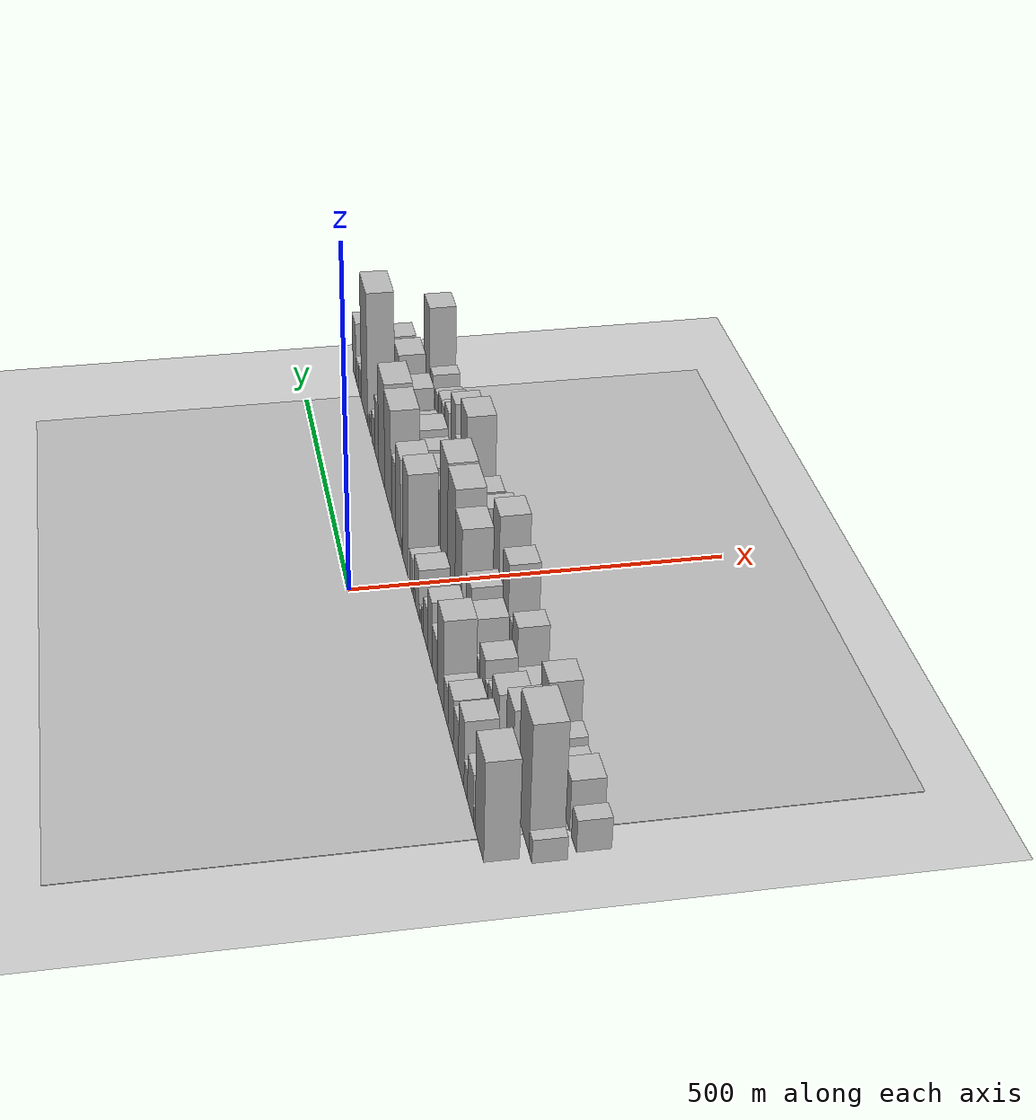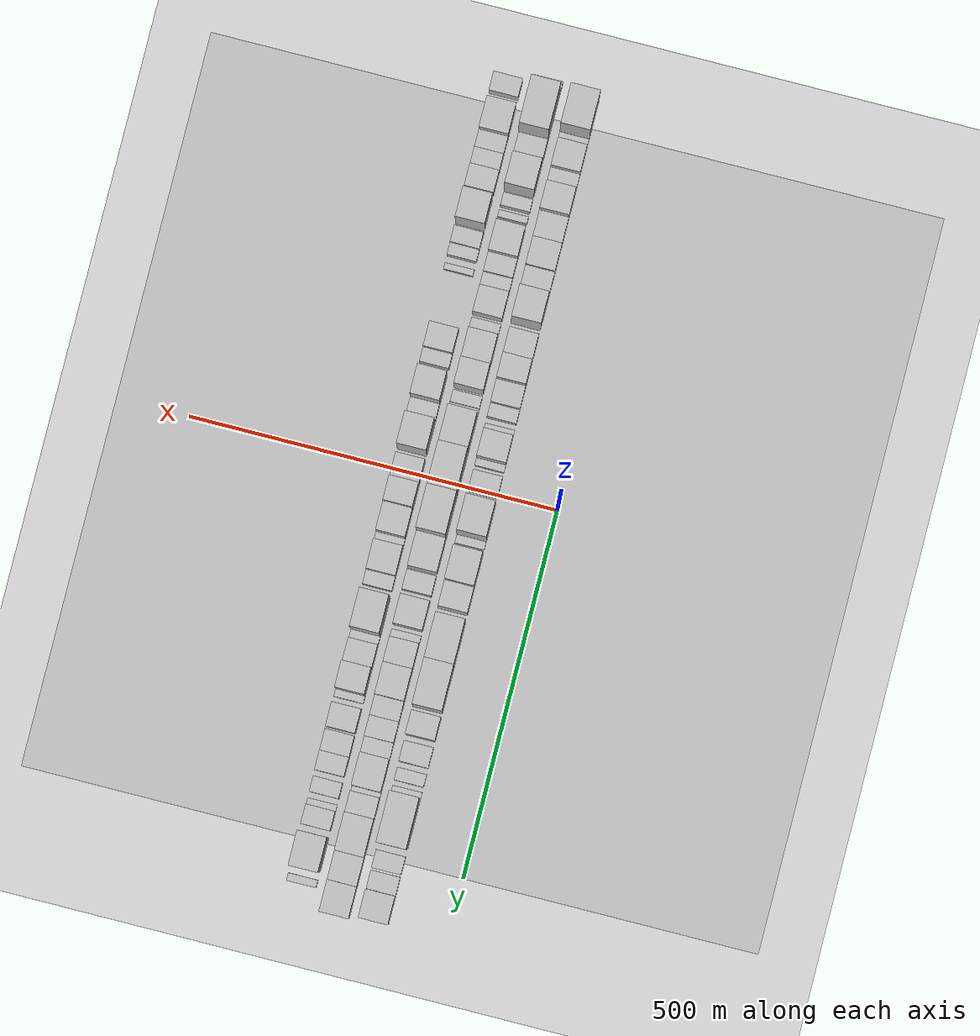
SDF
<?xml version="1.0" encoding="utf-8"?>

<sdf version="1.6">

   <world name="default">

      <gui fullscreen="0">

         <camera name="user_camera">

            <pose>-15 0 4.57585 0 0 0</pose>

            <view_controller>orbit</view_controller>

         </camera>

      </gui>

      <scene>

         <sky>

           <clouds>

             <speed>12</speed>

           </clouds>

         </sky>

         <ambient>0.4 0.4 0.4 1</ambient>

         <background>0.7 0.7 0.7 1</background>

         <shadows>1</shadows>

      </scene>

      <gravity>0 0 -9.8066</gravity>

      <magnetic_field>6e-06 2.3e-05 -4.2e-05</magnetic_field>

      <physics default="0" name="default_physics" type="ode">

         <ode>

            <solver>

               <type>quick</type>

               <iters>10</iters>

               <sor>1.0</sor>

               <use_dynamic_moi_rescaling>0</use_dynamic_moi_rescaling>

            </solver>

            <constraints>

               <cfm>0</cfm>

               <erp>0.2</erp>

               <contact_max_correcting_vel>100</contact_max_correcting_vel>

               <contact_surface_layer>0.001</contact_surface_layer>

            </constraints>

         </ode>

         <max_step_size>0.004</max_step_size>

         <real_time_factor>1</real_time_factor>

         <real_time_update_rate>250</real_time_update_rate>

      </physics>

      <light name="sun" type="directional">

         <cast_shadows>1</cast_shadows>

         <pose>0 0 10 0 0 0</pose>

         <diffuse>0.8 0.8 0.8 1</diffuse>

         <specular>0.2 0.2 0.2 1</specular>

         <attenuation>

            <range>1000</range>

            <constant>0.9</constant>

            <linear>0.01</linear>

            <quadratic>0.001</quadratic>

         </attenuation>

         <direction>-0.5 0.1 -0.9</direction>

      </light>

      <include>

         <name>ground_plane_1</name>

         <uri>model://HANNAS_ground_plane</uri>

         <pose>0 0 0  0 0 0</pose>

      </include>

      <include>

         <name>ground_plane_2</name>

         <uri>model://HANNAS_ground_plane</uri>

         <pose>100 0 0  0 0 0</pose>

      </include>

      <model name="building_1">

         <static>1</static>

         <pose frame="">100.0000 -510.8709 0 0.000000 0.000000 0.000000</pose>

         <link name="link">

            <pose frame="">0 0 70.50 0 0 0</pose>

            <collision name="collision">

               <geometry>

                  <box>

                     <size>40.0000 54.2581 141.0000</size>

                  </box>

               </geometry>

               <max_contacts>10</max_contacts>

               <surface>

                  <contact>

                     <ode/>

                  </contact>

                  <bounce/>

                  <friction>

                     <torsional>

                        <ode/>

                     </torsional>

                     <ode/>

                  </friction>

               </surface>

            </collision>

            <visual name="visual">

               <cast_shadows>0</cast_shadows>

               <geometry>

                  <box>

                     <size>40.0000 54.2581 141.0000</size>

                  </box>

               </geometry>

               <material>

                  <script>

                     <uri>model://HANNAS_wall/materials/scripts</uri>

                     <uri>model://HANNAS_wall/materials/textures</uri>

                     <name>vrc/HANNAS_wall</name>

                  </script>

               </material>

            </visual>

            <self_collide>0</self_collide>

            <enable_wind>0</enable_wind>

            <kinematic>0</kinematic>

         </link>

      </model>

      <model name="building_2">

         <static>1</static>

         <pose frame="">100.0000 -477.8455 0 0.000000 0.000000 0.000000</pose>

         <link name="link">

            <pose frame="">0 0 13.50 0 0 0</pose>

            <collision name="collision">

               <geometry>

                  <box>

                     <size>40.0000 11.7927 27.0000</size>

                  </box>

               </geometry>

               <max_contacts>10</max_contacts>

               <surface>

                  <contact>

                     <ode/>

                  </contact>

                  <bounce/>

                  <friction>

                     <torsional>

                        <ode/>

                     </torsional>

                     <ode/>

                  </friction>

               </surface>

            </collision>

            <visual name="visual">

               <cast_shadows>0</cast_shadows>

               <geometry>

                  <box>

                     <size>40.0000 11.7927 27.0000</size>

                  </box>

               </geometry>

               <material>

                  <script>

                     <uri>model://HANNAS_wall/materials/scripts</uri>

                     <uri>model://HANNAS_wall/materials/textures</uri>

                     <name>vrc/HANNAS_wall</name>

                  </script>

               </material>

            </visual>

            <self_collide>0</self_collide>

            <enable_wind>0</enable_wind>

            <kinematic>0</kinematic>

         </link>

      </model>

      <model name="building_3">

         <static>1</static>

         <pose frame="">100.0000 -453.1120 0 0.000000 0.000000 0.000000</pose>

         <link name="link">

            <pose frame="">0 0 34.50 0 0 0</pose>

            <collision name="collision">

               <geometry>

                  <box>

                     <size>40.0000 37.6744 69.0000</size>

                  </box>

               </geometry>

               <max_contacts>10</max_contacts>

               <surface>

                  <contact>

                     <ode/>

                  </contact>

                  <bounce/>

                  <friction>

                     <torsional>

                        <ode/>

                     </torsional>

                     <ode/>

                  </friction>

               </surface>

            </collision>

            <visual name="visual">

               <cast_shadows>0</cast_shadows>

               <geometry>

                  <box>

                     <size>40.0000 37.6744 69.0000</size>

                  </box>

               </geometry>

               <material>

                  <script>

                     <uri>model://HANNAS_wall/materials/scripts</uri>

                     <uri>model://HANNAS_wall/materials/textures</uri>

                     <name>vrc/HANNAS_wall</name>

                  </script>

               </material>

            </visual>

            <self_collide>0</self_collide>

            <enable_wind>0</enable_wind>

            <kinematic>0</kinematic>

         </link>

      </model>

      <model name="building_4">

         <static>1</static>

         <pose frame="">100.0000 -422.9121 0 0.000000 0.000000 0.000000</pose>

         <link name="link">

            <pose frame="">0 0 21.00 0 0 0</pose>

            <collision name="collision">

               <geometry>

                  <box>

                     <size>40.0000 22.7253 42.0000</size>

                  </box>

               </geometry>

               <max_contacts>10</max_contacts>

               <surface>

                  <contact>

                     <ode/>

                  </contact>

                  <bounce/>

                  <friction>

                     <torsional>

                        <ode/>

                     </torsional>

                     <ode/>

                  </friction>

               </surface>

            </collision>

            <visual name="visual">

               <cast_shadows>0</cast_shadows>

               <geometry>

                  <box>

                     <size>40.0000 22.7253 42.0000</size>

                  </box>

               </geometry>

               <material>

                  <script>

                     <uri>model://HANNAS_wall/materials/scripts</uri>

                     <uri>model://HANNAS_wall/materials/textures</uri>

                     <name>vrc/HANNAS_wall</name>

                  </script>

               </material>

            </visual>

            <self_collide>0</self_collide>

            <enable_wind>0</enable_wind>

            <kinematic>0</kinematic>

         </link>

      </model>

      <model name="building_5">

         <static>1</static>

         <pose frame="">100.0000 -392.6772 0 0.000000 0.000000 0.000000</pose>

         <link name="link">

            <pose frame="">0 0 48.00 0 0 0</pose>

            <collision name="collision">

               <geometry>

                  <box>

                     <size>40.0000 37.7445 96.0000</size>

                  </box>

               </geometry>

               <max_contacts>10</max_contacts>

               <surface>

                  <contact>

                     <ode/>

                  </contact>

                  <bounce/>

                  <friction>

                     <torsional>

                        <ode/>

                     </torsional>

                     <ode/>

                  </friction>

               </surface>

            </collision>

            <visual name="visual">

               <cast_shadows>0</cast_shadows>

               <geometry>

                  <box>

                     <size>40.0000 37.7445 96.0000</size>

                  </box>

               </geometry>

               <material>

                  <script>

                     <uri>model://HANNAS_wall/materials/scripts</uri>

                     <uri>model://HANNAS_wall/materials/textures</uri>

                     <name>vrc/HANNAS_wall</name>

                  </script>

               </material>

            </visual>

            <self_collide>0</self_collide>

            <enable_wind>0</enable_wind>

            <kinematic>0</kinematic>

         </link>

      </model>

      <model name="building_6">

         <static>1</static>

         <pose frame="">100.0000 -356.0114 0 0.000000 0.000000 0.000000</pose>

         <link name="link">

            <pose frame="">0 0 31.50 0 0 0</pose>

            <collision name="collision">

               <geometry>

                  <box>

                     <size>40.0000 35.5872 63.0000</size>

                  </box>

               </geometry>

               <max_contacts>10</max_contacts>

               <surface>

                  <contact>

                     <ode/>

                  </contact>

                  <bounce/>

                  <friction>

                     <torsional>

                        <ode/>

                     </torsional>

                     <ode/>

                  </friction>

               </surface>

            </collision>

            <visual name="visual">

               <cast_shadows>0</cast_shadows>

               <geometry>

                  <box>

                     <size>40.0000 35.5872 63.0000</size>

                  </box>

               </geometry>

               <material>

                  <script>

                     <uri>model://HANNAS_wall/materials/scripts</uri>

                     <uri>model://HANNAS_wall/materials/textures</uri>

                     <name>vrc/HANNAS_wall</name>

                  </script>

               </material>

            </visual>

            <self_collide>0</self_collide>

            <enable_wind>0</enable_wind>

            <kinematic>0</kinematic>

         </link>

      </model>

      <model name="building_7">

         <static>1</static>

         <pose frame="">100.0000 -319.1402 0 0.000000 0.000000 0.000000</pose>

         <link name="link">

            <pose frame="">0 0 34.50 0 0 0</pose>

            <collision name="collision">

               <geometry>

                  <box>

                     <size>40.0000 38.1551 69.0000</size>

                  </box>

               </geometry>

               <max_contacts>10</max_contacts>

               <surface>

                  <contact>

                     <ode/>

                  </contact>

                  <bounce/>

                  <friction>

                     <torsional>

                        <ode/>

                     </torsional>

                     <ode/>

                  </friction>

               </surface>

            </collision>

            <visual name="visual">

               <cast_shadows>0</cast_shadows>

               <geometry>

                  <box>

                     <size>40.0000 38.1551 69.0000</size>

                  </box>

               </geometry>

               <material>

                  <script>

                     <uri>model://HANNAS_wall/materials/scripts</uri>

                     <uri>model://HANNAS_wall/materials/textures</uri>

                     <name>vrc/HANNAS_wall</name>

                  </script>

               </material>

            </visual>

            <self_collide>0</self_collide>

            <enable_wind>0</enable_wind>

            <kinematic>0</kinematic>

         </link>

      </model>

      <model name="building_8">

         <static>1</static>

         <pose frame="">100.0000 -283.8798 0 0.000000 0.000000 0.000000</pose>

         <link name="link">

            <pose frame="">0 0 27.00 0 0 0</pose>

            <collision name="collision">

               <geometry>

                  <box>

                     <size>40.0000 32.3658 54.0000</size>

                  </box>

               </geometry>

               <max_contacts>10</max_contacts>

               <surface>

                  <contact>

                     <ode/>

                  </contact>

                  <bounce/>

                  <friction>

                     <torsional>

                        <ode/>

                     </torsional>

                     <ode/>

                  </friction>

               </surface>

            </collision>

            <visual name="visual">

               <cast_shadows>0</cast_shadows>

               <geometry>

                  <box>

                     <size>40.0000 32.3658 54.0000</size>

                  </box>

               </geometry>

               <material>

                  <script>

                     <uri>model://HANNAS_wall/materials/scripts</uri>

                     <uri>model://HANNAS_wall/materials/textures</uri>

                     <name>vrc/HANNAS_wall</name>

                  </script>

               </material>

            </visual>

            <self_collide>0</self_collide>

            <enable_wind>0</enable_wind>

            <kinematic>0</kinematic>

         </link>

      </model>

      <model name="building_9">

         <static>1</static>

         <pose frame="">100.0000 -245.9838 0 0.000000 0.000000 0.000000</pose>

         <link name="link">

            <pose frame="">0 0 66.00 0 0 0</pose>

            <collision name="collision">

               <geometry>

                  <box>

                     <size>40.0000 43.4262 132.0000</size>

                  </box>

               </geometry>

               <max_contacts>10</max_contacts>

               <surface>

                  <contact>

                     <ode/>

                  </contact>

                  <bounce/>

                  <friction>

                     <torsional>

                        <ode/>

                     </torsional>

                     <ode/>

                  </friction>

               </surface>

            </collision>

            <visual name="visual">

               <cast_shadows>0</cast_shadows>

               <geometry>

                  <box>

                     <size>40.0000 43.4262 132.0000</size>

                  </box>

               </geometry>

               <material>

                  <script>

                     <uri>model://HANNAS_wall/materials/scripts</uri>

                     <uri>model://HANNAS_wall/materials/textures</uri>

                     <name>vrc/HANNAS_wall</name>

                  </script>

               </material>

            </visual>

            <self_collide>0</self_collide>

            <enable_wind>0</enable_wind>

            <kinematic>0</kinematic>

         </link>

      </model>

      <model name="building_10">

         <static>1</static>

         <pose frame="">100.0000 -197.0725 0 0.000000 0.000000 0.000000</pose>

         <link name="link">

            <pose frame="">0 0 33.00 0 0 0</pose>

            <collision name="collision">

               <geometry>

                  <box>

                     <size>40.0000 36.3964 66.0000</size>

                  </box>

               </geometry>

               <max_contacts>10</max_contacts>

               <surface>

                  <contact>

                     <ode/>

                  </contact>

                  <bounce/>

                  <friction>

                     <torsional>

                        <ode/>

                     </torsional>

                     <ode/>

                  </friction>

               </surface>

            </collision>

            <visual name="visual">

               <cast_shadows>0</cast_shadows>

               <geometry>

                  <box>

                     <size>40.0000 36.3964 66.0000</size>

                  </box>

               </geometry>

               <material>

                  <script>

                     <uri>model://HANNAS_wall/materials/scripts</uri>

                     <uri>model://HANNAS_wall/materials/textures</uri>

                     <name>vrc/HANNAS_wall</name>

                  </script>

               </material>

            </visual>

            <self_collide>0</self_collide>

            <enable_wind>0</enable_wind>

            <kinematic>0</kinematic>

         </link>

      </model>

      <model name="building_11">

         <static>1</static>

         <pose frame="">100.0000 -162.0324 0 0.000000 0.000000 0.000000</pose>

         <link name="link">

            <pose frame="">0 0 48.00 0 0 0</pose>

            <collision name="collision">

               <geometry>

                  <box>

                     <size>40.0000 33.6838 96.0000</size>

                  </box>

               </geometry>

               <max_contacts>10</max_contacts>

               <surface>

                  <contact>

                     <ode/>

                  </contact>

                  <bounce/>

                  <friction>

                     <torsional>

                        <ode/>

                     </torsional>

                     <ode/>

                  </friction>

               </surface>

            </collision>

            <visual name="visual">

               <cast_shadows>0</cast_shadows>

               <geometry>

                  <box>

                     <size>40.0000 33.6838 96.0000</size>

                  </box>

               </geometry>

               <material>

                  <script>

                     <uri>model://HANNAS_wall/materials/scripts</uri>

                     <uri>model://HANNAS_wall/materials/textures</uri>

                     <name>vrc/HANNAS_wall</name>

                  </script>

               </material>

            </visual>

            <self_collide>0</self_collide>

            <enable_wind>0</enable_wind>

            <kinematic>0</kinematic>

         </link>

      </model>

      <model name="building_12">

         <static>1</static>

         <pose frame="">100.0000 -129.7146 0 0.000000 0.000000 0.000000</pose>

         <link name="link">

            <pose frame="">0 0 30.00 0 0 0</pose>

            <collision name="collision">

               <geometry>

                  <box>

                     <size>40.0000 30.9517 60.0000</size>

                  </box>

               </geometry>

               <max_contacts>10</max_contacts>

               <surface>

                  <contact>

                     <ode/>

                  </contact>

                  <bounce/>

                  <friction>

                     <torsional>

                        <ode/>

                     </torsional>

                     <ode/>

                  </friction>

               </surface>

            </collision>

            <visual name="visual">

               <cast_shadows>0</cast_shadows>

               <geometry>

                  <box>

                     <size>40.0000 30.9517 60.0000</size>

                  </box>

               </geometry>

               <material>

                  <script>

                     <uri>model://HANNAS_wall/materials/scripts</uri>

                     <uri>model://HANNAS_wall/materials/textures</uri>

                     <name>vrc/HANNAS_wall</name>

                  </script>

               </material>

            </visual>

            <self_collide>0</self_collide>

            <enable_wind>0</enable_wind>

            <kinematic>0</kinematic>

         </link>

      </model>

      <model name="building_13">

         <static>1</static>

         <pose frame="">100.0000 -104.8433 0 0.000000 0.000000 0.000000</pose>

         <link name="link">

            <pose frame="">0 0 18.00 0 0 0</pose>

            <collision name="collision">

               <geometry>

                  <box>

                     <size>40.0000 18.7910 36.0000</size>

                  </box>

               </geometry>

               <max_contacts>10</max_contacts>

               <surface>

                  <contact>

                     <ode/>

                  </contact>

                  <bounce/>

                  <friction>

                     <torsional>

                        <ode/>

                     </torsional>

                     <ode/>

                  </friction>

               </surface>

            </collision>

            <visual name="visual">

               <cast_shadows>0</cast_shadows>

               <geometry>

                  <box>

                     <size>40.0000 18.7910 36.0000</size>

                  </box>

               </geometry>

               <material>

                  <script>

                     <uri>model://HANNAS_wall/materials/scripts</uri>

                     <uri>model://HANNAS_wall/materials/textures</uri>

                     <name>vrc/HANNAS_wall</name>

                  </script>

               </material>

            </visual>

            <self_collide>0</self_collide>

            <enable_wind>0</enable_wind>

            <kinematic>0</kinematic>

         </link>

      </model>

      <model name="building_14">

         <static>1</static>

         <pose frame="">100.0000 -82.6187 0 0.000000 0.000000 0.000000</pose>

         <link name="link">

            <pose frame="">0 0 10.50 0 0 0</pose>

            <collision name="collision">

               <geometry>

                  <box>

                     <size>40.0000 9.6580 21.0000</size>

                  </box>

               </geometry>

               <max_contacts>10</max_contacts>

               <surface>

                  <contact>

                     <ode/>

                  </contact>

                  <bounce/>

                  <friction>

                     <torsional>

                        <ode/>

                     </torsional>

                     <ode/>

                  </friction>

               </surface>

            </collision>

            <visual name="visual">

               <cast_shadows>0</cast_shadows>

               <geometry>

                  <box>

                     <size>40.0000 9.6580 21.0000</size>

                  </box>

               </geometry>

               <material>

                  <script>

                     <uri>model://HANNAS_wall/materials/scripts</uri>

                     <uri>model://HANNAS_wall/materials/textures</uri>

                     <name>vrc/HANNAS_wall</name>

                  </script>

               </material>

            </visual>

            <self_collide>0</self_collide>

            <enable_wind>0</enable_wind>

            <kinematic>0</kinematic>

         </link>

      </model>

      <model name="building_15">

         <static>1</static>

         <pose frame="">100.0000 -58.9657 0 0.000000 0.000000 0.000000</pose>

         <link name="link">

            <pose frame="">0 0 37.50 0 0 0</pose>

            <collision name="collision">

               <geometry>

                  <box>

                     <size>40.0000 37.6481 75.0000</size>

                  </box>

               </geometry>

               <max_contacts>10</max_contacts>

               <surface>

                  <contact>

                     <ode/>

                  </contact>

                  <bounce/>

                  <friction>

                     <torsional>

                        <ode/>

                     </torsional>

                     <ode/>

                  </friction>

               </surface>

            </collision>

            <visual name="visual">

               <cast_shadows>0</cast_shadows>

               <geometry>

                  <box>

                     <size>40.0000 37.6481 75.0000</size>

                  </box>

               </geometry>

               <material>

                  <script>

                     <uri>model://HANNAS_wall/materials/scripts</uri>

                     <uri>model://HANNAS_wall/materials/textures</uri>

                     <name>vrc/HANNAS_wall</name>

                  </script>

               </material>

            </visual>

            <self_collide>0</self_collide>

            <enable_wind>0</enable_wind>

            <kinematic>0</kinematic>

         </link>

      </model>

      <model name="building_16">

         <static>1</static>

         <pose frame="">100.0000 -35.0125 0 0.000000 0.000000 0.000000</pose>

         <link name="link">

            <pose frame="">0 0 10.50 0 0 0</pose>

            <collision name="collision">

               <geometry>

                  <box>

                     <size>40.0000 10.2582 21.0000</size>

                  </box>

               </geometry>

               <max_contacts>10</max_contacts>

               <surface>

                  <contact>

                     <ode/>

                  </contact>

                  <bounce/>

                  <friction>

                     <torsional>

                        <ode/>

                     </torsional>

                     <ode/>

                  </friction>

               </surface>

            </collision>

            <visual name="visual">

               <cast_shadows>0</cast_shadows>

               <geometry>

                  <box>

                     <size>40.0000 10.2582 21.0000</size>

                  </box>

               </geometry>

               <material>

                  <script>

                     <uri>model://HANNAS_wall/materials/scripts</uri>

                     <uri>model://HANNAS_wall/materials/textures</uri>

                     <name>vrc/HANNAS_wall</name>

                  </script>

               </material>

            </visual>

            <self_collide>0</self_collide>

            <enable_wind>0</enable_wind>

            <kinematic>0</kinematic>

         </link>

      </model>

      <model name="building_17">

         <static>1</static>

         <pose frame="">100.0000 -8.8030 0 0.000000 0.000000 0.000000</pose>

         <link name="link">

            <pose frame="">0 0 27.00 0 0 0</pose>

            <collision name="collision">

               <geometry>

                  <box>

                     <size>40.0000 28.1608 54.0000</size>

                  </box>

               </geometry>

               <max_contacts>10</max_contacts>

               <surface>

                  <contact>

                     <ode/>

                  </contact>

                  <bounce/>

                  <friction>

                     <torsional>

                        <ode/>

                     </torsional>

                     <ode/>

                  </friction>

               </surface>

            </collision>

            <visual name="visual">

               <cast_shadows>0</cast_shadows>

               <geometry>

                  <box>

                     <size>40.0000 28.1608 54.0000</size>

                  </box>

               </geometry>

               <material>

                  <script>

                     <uri>model://HANNAS_wall/materials/scripts</uri>

                     <uri>model://HANNAS_wall/materials/textures</uri>

                     <name>vrc/HANNAS_wall</name>

                  </script>

               </material>

            </visual>

            <self_collide>0</self_collide>

            <enable_wind>0</enable_wind>

            <kinematic>0</kinematic>

         </link>

      </model>

      <model name="building_18">

         <static>1</static>

         <pose frame="">100.0000 39.7489 0 0.000000 0.000000 0.000000</pose>

         <link name="link">

            <pose frame="">0 0 79.50 0 0 0</pose>

            <collision name="collision">

               <geometry>

                  <box>

                     <size>40.0000 48.9430 159.0000</size>

                  </box>

               </geometry>

               <max_contacts>10</max_contacts>

               <surface>

                  <contact>

                     <ode/>

                  </contact>

                  <bounce/>

                  <friction>

                     <torsional>

                        <ode/>

                     </torsional>

                     <ode/>

                  </friction>

               </surface>

            </collision>

            <visual name="visual">

               <cast_shadows>0</cast_shadows>

               <geometry>

                  <box>

                     <size>40.0000 48.9430 159.0000</size>

                  </box>

               </geometry>

               <material>

                  <script>

                     <uri>model://HANNAS_wall/materials/scripts</uri>

                     <uri>model://HANNAS_wall/materials/textures</uri>

                     <name>vrc/HANNAS_wall</name>

                  </script>

               </material>

            </visual>

            <self_collide>0</self_collide>

            <enable_wind>0</enable_wind>

            <kinematic>0</kinematic>

         </link>

      </model>

      <model name="building_19">

         <static>1</static>

         <pose frame="">100.0000 69.9197 0 0.000000 0.000000 0.000000</pose>

         <link name="link">

            <pose frame="">0 0 13.50 0 0 0</pose>

            <collision name="collision">

               <geometry>

                  <box>

                     <size>40.0000 11.3985 27.0000</size>

                  </box>

               </geometry>

               <max_contacts>10</max_contacts>

               <surface>

                  <contact>

                     <ode/>

                  </contact>

                  <bounce/>

                  <friction>

                     <torsional>

                        <ode/>

                     </torsional>

                     <ode/>

                  </friction>

               </surface>

            </collision>

            <visual name="visual">

               <cast_shadows>0</cast_shadows>

               <geometry>

                  <box>

                     <size>40.0000 11.3985 27.0000</size>

                  </box>

               </geometry>

               <material>

                  <script>

                     <uri>model://HANNAS_wall/materials/scripts</uri>

                     <uri>model://HANNAS_wall/materials/textures</uri>

                     <name>vrc/HANNAS_wall</name>

                  </script>

               </material>

            </visual>

            <self_collide>0</self_collide>

            <enable_wind>0</enable_wind>

            <kinematic>0</kinematic>

         </link>

      </model>

      <model name="building_20">

         <static>1</static>

         <pose frame="">100.0000 105.6717 0 0.000000 0.000000 0.000000</pose>

         <link name="link">

            <pose frame="">0 0 70.50 0 0 0</pose>

            <collision name="collision">

               <geometry>

                  <box>

                     <size>40.0000 46.1056 141.0000</size>

                  </box>

               </geometry>

               <max_contacts>10</max_contacts>

               <surface>

                  <contact>

                     <ode/>

                  </contact>

                  <bounce/>

                  <friction>

                     <torsional>

                        <ode/>

                     </torsional>

                     <ode/>

                  </friction>

               </surface>

            </collision>

            <visual name="visual">

               <cast_shadows>0</cast_shadows>

               <geometry>

                  <box>

                     <size>40.0000 46.1056 141.0000</size>

                  </box>

               </geometry>

               <material>

                  <script>

                     <uri>model://HANNAS_wall/materials/scripts</uri>

                     <uri>model://HANNAS_wall/materials/textures</uri>

                     <name>vrc/HANNAS_wall</name>

                  </script>

               </material>

            </visual>

            <self_collide>0</self_collide>

            <enable_wind>0</enable_wind>

            <kinematic>0</kinematic>

         </link>

      </model>

      <model name="building_21">

         <static>1</static>

         <pose frame="">100.0000 146.2361 0 0.000000 0.000000 0.000000</pose>

         <link name="link">

            <pose frame="">0 0 51.00 0 0 0</pose>

            <collision name="collision">

               <geometry>

                  <box>

                     <size>40.0000 35.0231 102.0000</size>

                  </box>

               </geometry>

               <max_contacts>10</max_contacts>

               <surface>

                  <contact>

                     <ode/>

                  </contact>

                  <bounce/>

                  <friction>

                     <torsional>

                        <ode/>

                     </torsional>

                     <ode/>

                  </friction>

               </surface>

            </collision>

            <visual name="visual">

               <cast_shadows>0</cast_shadows>

               <geometry>

                  <box>

                     <size>40.0000 35.0231 102.0000</size>

                  </box>

               </geometry>

               <material>

                  <script>

                     <uri>model://HANNAS_wall/materials/scripts</uri>

                     <uri>model://HANNAS_wall/materials/textures</uri>

                     <name>vrc/HANNAS_wall</name>

                  </script>

               </material>

            </visual>

            <self_collide>0</self_collide>

            <enable_wind>0</enable_wind>

            <kinematic>0</kinematic>

         </link>

      </model>

      <model name="building_22">

         <static>1</static>

         <pose frame="">100.0000 204.1579 0 0.000000 0.000000 0.000000</pose>

         <link name="link">

            <pose frame="">0 0 81.00 0 0 0</pose>

            <collision name="collision">

               <geometry>

                  <box>

                     <size>40.0000 60.8206 162.0000</size>

                  </box>

               </geometry>

               <max_contacts>10</max_contacts>

               <surface>

                  <contact>

                     <ode/>

                  </contact>

                  <bounce/>

                  <friction>

                     <torsional>

                        <ode/>

                     </torsional>

                     <ode/>

                  </friction>

               </surface>

            </collision>

            <visual name="visual">

               <cast_shadows>0</cast_shadows>

               <geometry>

                  <box>

                     <size>40.0000 60.8206 162.0000</size>

                  </box>

               </geometry>

               <material>

                  <script>

                     <uri>model://HANNAS_wall/materials/scripts</uri>

                     <uri>model://HANNAS_wall/materials/textures</uri>

                     <name>vrc/HANNAS_wall</name>

                  </script>

               </material>

            </visual>

            <self_collide>0</self_collide>

            <enable_wind>0</enable_wind>

            <kinematic>0</kinematic>

         </link>

      </model>

      <model name="building_23">

         <static>1</static>

         <pose frame="">100.0000 265.8493 0 0.000000 0.000000 0.000000</pose>

         <link name="link">

            <pose frame="">0 0 84.00 0 0 0</pose>

            <collision name="collision">

               <geometry>

                  <box>

                     <size>40.0000 62.5623 168.0000</size>

                  </box>

               </geometry>

               <max_contacts>10</max_contacts>

               <surface>

                  <contact>

                     <ode/>

                  </contact>

                  <bounce/>

                  <friction>

                     <torsional>

                        <ode/>

                     </torsional>

                     <ode/>

                  </friction>

               </surface>

            </collision>

            <visual name="visual">

               <cast_shadows>0</cast_shadows>

               <geometry>

                  <box>

                     <size>40.0000 62.5623 168.0000</size>

                  </box>

               </geometry>

               <material>

                  <script>

                     <uri>model://HANNAS_wall/materials/scripts</uri>

                     <uri>model://HANNAS_wall/materials/textures</uri>

                     <name>vrc/HANNAS_wall</name>

                  </script>

               </material>

            </visual>

            <self_collide>0</self_collide>

            <enable_wind>0</enable_wind>

            <kinematic>0</kinematic>

         </link>

      </model>

      <model name="building_24">

         <static>1</static>

         <pose frame="">100.0000 319.2803 0 0.000000 0.000000 0.000000</pose>

         <link name="link">

            <pose frame="">0 0 48.00 0 0 0</pose>

            <collision name="collision">

               <geometry>

                  <box>

                     <size>40.0000 32.2996 96.0000</size>

                  </box>

               </geometry>

               <max_contacts>10</max_contacts>

               <surface>

                  <contact>

                     <ode/>

                  </contact>

                  <bounce/>

                  <friction>

                     <torsional>

                        <ode/>

                     </torsional>

                     <ode/>

                  </friction>

               </surface>

            </collision>

            <visual name="visual">

               <cast_shadows>0</cast_shadows>

               <geometry>

                  <box>

                     <size>40.0000 32.2996 96.0000</size>

                  </box>

               </geometry>

               <material>

                  <script>

                     <uri>model://HANNAS_wall/materials/scripts</uri>

                     <uri>model://HANNAS_wall/materials/textures</uri>

                     <name>vrc/HANNAS_wall</name>

                  </script>

               </material>

            </visual>

            <self_collide>0</self_collide>

            <enable_wind>0</enable_wind>

            <kinematic>0</kinematic>

         </link>

      </model>

      <model name="building_25">

         <static>1</static>

         <pose frame="">100.0000 357.4928 0 0.000000 0.000000 0.000000</pose>

         <link name="link">

            <pose frame="">0 0 25.50 0 0 0</pose>

            <collision name="collision">

               <geometry>

                  <box>

                     <size>40.0000 28.1254 51.0000</size>

                  </box>

               </geometry>

               <max_contacts>10</max_contacts>

               <surface>

                  <contact>

                     <ode/>

                  </contact>

                  <bounce/>

                  <friction>

                     <torsional>

                        <ode/>

                     </torsional>

                     <ode/>

                  </friction>

               </surface>

            </collision>

            <visual name="visual">

               <cast_shadows>0</cast_shadows>

               <geometry>

                  <box>

                     <size>40.0000 28.1254 51.0000</size>

                  </box>

               </geometry>

               <material>

                  <script>

                     <uri>model://HANNAS_wall/materials/scripts</uri>

                     <uri>model://HANNAS_wall/materials/textures</uri>

                     <name>vrc/HANNAS_wall</name>

                  </script>

               </material>

            </visual>

            <self_collide>0</self_collide>

            <enable_wind>0</enable_wind>

            <kinematic>0</kinematic>

         </link>

      </model>

      <model name="building_26">

         <static>1</static>

         <pose frame="">100.0000 388.2143 0 0.000000 0.000000 0.000000</pose>

         <link name="link">

            <pose frame="">0 0 16.50 0 0 0</pose>

            <collision name="collision">

               <geometry>

                  <box>

                     <size>40.0000 17.3176 33.0000</size>

                  </box>

               </geometry>

               <max_contacts>10</max_contacts>

               <surface>

                  <contact>

                     <ode/>

                  </contact>

                  <bounce/>

                  <friction>

                     <torsional>

                        <ode/>

                     </torsional>

                     <ode/>

                  </friction>

               </surface>

            </collision>

            <visual name="visual">

               <cast_shadows>0</cast_shadows>

               <geometry>

                  <box>

                     <size>40.0000 17.3176 33.0000</size>

                  </box>

               </geometry>

               <material>

                  <script>

                     <uri>model://HANNAS_wall/materials/scripts</uri>

                     <uri>model://HANNAS_wall/materials/textures</uri>

                     <name>vrc/HANNAS_wall</name>

                  </script>

               </material>

            </visual>

            <self_collide>0</self_collide>

            <enable_wind>0</enable_wind>

            <kinematic>0</kinematic>

         </link>

      </model>

      <model name="building_27">

         <static>1</static>

         <pose frame="">100.0000 408.3198 0 0.000000 0.000000 0.000000</pose>

         <link name="link">

            <pose frame="">0 0 10.50 0 0 0</pose>

            <collision name="collision">

               <geometry>

                  <box>

                     <size>40.0000 8.8934 21.0000</size>

                  </box>

               </geometry>

               <max_contacts>10</max_contacts>

               <surface>

                  <contact>

                     <ode/>

                  </contact>

                  <bounce/>

                  <friction>

                     <torsional>

                        <ode/>

                     </torsional>

                     <ode/>

                  </friction>

               </surface>

            </collision>

            <visual name="visual">

               <cast_shadows>0</cast_shadows>

               <geometry>

                  <box>

                     <size>40.0000 8.8934 21.0000</size>

                  </box>

               </geometry>

               <material>

                  <script>

                     <uri>model://HANNAS_wall/materials/scripts</uri>

                     <uri>model://HANNAS_wall/materials/textures</uri>

                     <name>vrc/HANNAS_wall</name>

                  </script>

               </material>

            </visual>

            <self_collide>0</self_collide>

            <enable_wind>0</enable_wind>

            <kinematic>0</kinematic>

         </link>

      </model>

      <model name="building_28">

         <static>1</static>

         <pose frame="">100.0000 447.2797 0 0.000000 0.000000 0.000000</pose>

         <link name="link">

            <pose frame="">0 0 108.00 0 0 0</pose>

            <collision name="collision">

               <geometry>

                  <box>

                     <size>40.0000 69.0263 216.0000</size>

                  </box>

               </geometry>

               <max_contacts>10</max_contacts>

               <surface>

                  <contact>

                     <ode/>

                  </contact>

                  <bounce/>

                  <friction>

                     <torsional>

                        <ode/>

                     </torsional>

                     <ode/>

                  </friction>

               </surface>

            </collision>

            <visual name="visual">

               <cast_shadows>0</cast_shadows>

               <geometry>

                  <box>

                     <size>40.0000 69.0263 216.0000</size>

                  </box>

               </geometry>

               <material>

                  <script>

                     <uri>model://HANNAS_wall/materials/scripts</uri>

                     <uri>model://HANNAS_wall/materials/textures</uri>

                     <name>vrc/HANNAS_wall</name>

                  </script>

               </material>

            </visual>

            <self_collide>0</self_collide>

            <enable_wind>0</enable_wind>

            <kinematic>0</kinematic>

         </link>

      </model>

      <model name="building_29">

         <static>1</static>

         <pose frame="">100.0000 503.0790 0 0.000000 0.000000 0.000000</pose>

         <link name="link">

            <pose frame="">0 0 24.00 0 0 0</pose>

            <collision name="collision">

               <geometry>

                  <box>

                     <size>40.0000 24.5723 48.0000</size>

                  </box>

               </geometry>

               <max_contacts>10</max_contacts>

               <surface>

                  <contact>

                     <ode/>

                  </contact>

                  <bounce/>

                  <friction>

                     <torsional>

                        <ode/>

                     </torsional>

                     <ode/>

                  </friction>

               </surface>

            </collision>

            <visual name="visual">

               <cast_shadows>0</cast_shadows>

               <geometry>

                  <box>

                     <size>40.0000 24.5723 48.0000</size>

                  </box>

               </geometry>

               <material>

                  <script>

                     <uri>model://HANNAS_wall/materials/scripts</uri>

                     <uri>model://HANNAS_wall/materials/textures</uri>

                     <name>vrc/HANNAS_wall</name>

                  </script>

               </material>

            </visual>

            <self_collide>0</self_collide>

            <enable_wind>0</enable_wind>

            <kinematic>0</kinematic>

         </link>

      </model>

      <model name="building_30">

         <static>1</static>

         <pose frame="">100.0000 531.0249 0 0.000000 0.000000 0.000000</pose>

         <link name="link">

            <pose frame="">0 0 22.50 0 0 0</pose>

            <collision name="collision">

               <geometry>

                  <box>

                     <size>40.0000 25.3195 45.0000</size>

                  </box>

               </geometry>

               <max_contacts>10</max_contacts>

               <surface>

                  <contact>

                     <ode/>

                  </contact>

                  <bounce/>

                  <friction>

                     <torsional>

                        <ode/>

                     </torsional>

                     <ode/>

                  </friction>

               </surface>

            </collision>

            <visual name="visual">

               <cast_shadows>0</cast_shadows>

               <geometry>

                  <box>

                     <size>40.0000 25.3195 45.0000</size>

                  </box>

               </geometry>

               <material>

                  <script>

                     <uri>model://HANNAS_wall/materials/scripts</uri>

                     <uri>model://HANNAS_wall/materials/textures</uri>

                     <name>vrc/HANNAS_wall</name>

                  </script>

               </material>

            </visual>

            <self_collide>0</self_collide>

            <enable_wind>0</enable_wind>

            <kinematic>0</kinematic>

         </link>

      </model>

      <model name="building_31">

         <static>1</static>

         <pose frame="">100.0000 562.9682 0 0.000000 0.000000 0.000000</pose>

         <link name="link">

            <pose frame="">0 0 49.50 0 0 0</pose>

            <collision name="collision">

               <geometry>

                  <box>

                     <size>40.0000 38.5670 99.0000</size>

                  </box>

               </geometry>

               <max_contacts>10</max_contacts>

               <surface>

                  <contact>

                     <ode/>

                  </contact>

                  <bounce/>

                  <friction>

                     <torsional>

                        <ode/>

                     </torsional>

                     <ode/>

                  </friction>

               </surface>

            </collision>

            <visual name="visual">

               <cast_shadows>0</cast_shadows>

               <geometry>

                  <box>

                     <size>40.0000 38.5670 99.0000</size>

                  </box>

               </geometry>

               <material>

                  <script>

                     <uri>model://HANNAS_wall/materials/scripts</uri>

                     <uri>model://HANNAS_wall/materials/textures</uri>

                     <name>vrc/HANNAS_wall</name>

                  </script>

               </material>

            </visual>

            <self_collide>0</self_collide>

            <enable_wind>0</enable_wind>

            <kinematic>0</kinematic>

         </link>

      </model>

      <model name="building_32">

         <static>1</static>

         <pose frame="">152.0000 -539.6510 0 0.000000 0.000000 0.000000</pose>

         <link name="link">

            <pose frame="">0 0 16.50 0 0 0</pose>

            <collision name="collision">

               <geometry>

                  <box>

                     <size>40.0000 16.6979 33.0000</size>

                  </box>

               </geometry>

               <max_contacts>10</max_contacts>

               <surface>

                  <contact>

                     <ode/>

                  </contact>

                  <bounce/>

                  <friction>

                     <torsional>

                        <ode/>

                     </torsional>

                     <ode/>

                  </friction>

               </surface>

            </collision>

            <visual name="visual">

               <cast_shadows>0</cast_shadows>

               <geometry>

                  <box>

                     <size>40.0000 16.6979 33.0000</size>

                  </box>

               </geometry>

               <material>

                  <script>

                     <uri>model://HANNAS_wall/materials/scripts</uri>

                     <uri>model://HANNAS_wall/materials/textures</uri>

                     <name>vrc/HANNAS_wall</name>

                  </script>

               </material>

            </visual>

            <self_collide>0</self_collide>

            <enable_wind>0</enable_wind>

            <kinematic>0</kinematic>

         </link>

      </model>

      <model name="building_33">

         <static>1</static>

         <pose frame="">152.0000 -499.0679 0 0.000000 0.000000 0.000000</pose>

         <link name="link">

            <pose frame="">0 0 90.00 0 0 0</pose>

            <collision name="collision">

               <geometry>

                  <box>

                     <size>40.0000 64.4685 180.0000</size>

                  </box>

               </geometry>

               <max_contacts>10</max_contacts>

               <surface>

                  <contact>

                     <ode/>

                  </contact>

                  <bounce/>

                  <friction>

                     <torsional>

                        <ode/>

                     </torsional>

                     <ode/>

                  </friction>

               </surface>

            </collision>

            <visual name="visual">

               <cast_shadows>0</cast_shadows>

               <geometry>

                  <box>

                     <size>40.0000 64.4685 180.0000</size>

                  </box>

               </geometry>

               <material>

                  <script>

                     <uri>model://HANNAS_wall/materials/scripts</uri>

                     <uri>model://HANNAS_wall/materials/textures</uri>

                     <name>vrc/HANNAS_wall</name>

                  </script>

               </material>

            </visual>

            <self_collide>0</self_collide>

            <enable_wind>0</enable_wind>

            <kinematic>0</kinematic>

         </link>

      </model>

      <model name="building_34">

         <static>1</static>

         <pose frame="">152.0000 -450.8416 0 0.000000 0.000000 0.000000</pose>

         <link name="link">

            <pose frame="">0 0 30.00 0 0 0</pose>

            <collision name="collision">

               <geometry>

                  <box>

                     <size>40.0000 31.9840 60.0000</size>

                  </box>

               </geometry>

               <max_contacts>10</max_contacts>

               <surface>

                  <contact>

                     <ode/>

                  </contact>

                  <bounce/>

                  <friction>

                     <torsional>

                        <ode/>

                     </torsional>

                     <ode/>

                  </friction>

               </surface>

            </collision>

            <visual name="visual">

               <cast_shadows>0</cast_shadows>

               <geometry>

                  <box>

                     <size>40.0000 31.9840 60.0000</size>

                  </box>

               </geometry>

               <material>

                  <script>

                     <uri>model://HANNAS_wall/materials/scripts</uri>

                     <uri>model://HANNAS_wall/materials/textures</uri>

                     <name>vrc/HANNAS_wall</name>

                  </script>

               </material>

            </visual>

            <self_collide>0</self_collide>

            <enable_wind>0</enable_wind>

            <kinematic>0</kinematic>

         </link>

      </model>

      <model name="building_35">

         <static>1</static>

         <pose frame="">152.0000 -413.2766 0 0.000000 0.000000 0.000000</pose>

         <link name="link">

            <pose frame="">0 0 61.50 0 0 0</pose>

            <collision name="collision">

               <geometry>

                  <box>

                     <size>40.0000 43.1460 123.0000</size>

                  </box>

               </geometry>

               <max_contacts>10</max_contacts>

               <surface>

                  <contact>

                     <ode/>

                  </contact>

                  <bounce/>

                  <friction>

                     <torsional>

                        <ode/>

                     </torsional>

                     <ode/>

                  </friction>

               </surface>

            </collision>

            <visual name="visual">

               <cast_shadows>0</cast_shadows>

               <geometry>

                  <box>

                     <size>40.0000 43.1460 123.0000</size>

                  </box>

               </geometry>

               <material>

                  <script>

                     <uri>model://HANNAS_wall/materials/scripts</uri>

                     <uri>model://HANNAS_wall/materials/textures</uri>

                     <name>vrc/HANNAS_wall</name>

                  </script>

               </material>

            </visual>

            <self_collide>0</self_collide>

            <enable_wind>0</enable_wind>

            <kinematic>0</kinematic>

         </link>

      </model>

      <model name="building_36">

         <static>1</static>

         <pose frame="">152.0000 -378.8482 0 0.000000 0.000000 0.000000</pose>

         <link name="link">

            <pose frame="">0 0 16.50 0 0 0</pose>

            <collision name="collision">

               <geometry>

                  <box>

                     <size>40.0000 17.7106 33.0000</size>

                  </box>

               </geometry>

               <max_contacts>10</max_contacts>

               <surface>

                  <contact>

                     <ode/>

                  </contact>

                  <bounce/>

                  <friction>

                     <torsional>

                        <ode/>

                     </torsional>

                     <ode/>

                  </friction>

               </surface>

            </collision>

            <visual name="visual">

               <cast_shadows>0</cast_shadows>

               <geometry>

                  <box>

                     <size>40.0000 17.7106 33.0000</size>

                  </box>

               </geometry>

               <material>

                  <script>

                     <uri>model://HANNAS_wall/materials/scripts</uri>

                     <uri>model://HANNAS_wall/materials/textures</uri>

                     <name>vrc/HANNAS_wall</name>

                  </script>

               </material>

            </visual>

            <self_collide>0</self_collide>

            <enable_wind>0</enable_wind>

            <kinematic>0</kinematic>

         </link>

      </model>

      <model name="building_37">

         <static>1</static>

         <pose frame="">152.0000 -360.1530 0 0.000000 0.000000 0.000000</pose>

         <link name="link">

            <pose frame="">0 0 10.50 0 0 0</pose>

            <collision name="collision">

               <geometry>

                  <box>

                     <size>40.0000 9.6798 21.0000</size>

                  </box>

               </geometry>

               <max_contacts>10</max_contacts>

               <surface>

                  <contact>

                     <ode/>

                  </contact>

                  <bounce/>

                  <friction>

                     <torsional>

                        <ode/>

                     </torsional>

                     <ode/>

                  </friction>

               </surface>

            </collision>

            <visual name="visual">

               <cast_shadows>0</cast_shadows>

               <geometry>

                  <box>

                     <size>40.0000 9.6798 21.0000</size>

                  </box>

               </geometry>

               <material>

                  <script>

                     <uri>model://HANNAS_wall/materials/scripts</uri>

                     <uri>model://HANNAS_wall/materials/textures</uri>

                     <name>vrc/HANNAS_wall</name>

                  </script>

               </material>

            </visual>

            <self_collide>0</self_collide>

            <enable_wind>0</enable_wind>

            <kinematic>0</kinematic>

         </link>

      </model>

      <model name="building_38">

         <static>1</static>

         <pose frame="">152.0000 -326.4027 0 0.000000 0.000000 0.000000</pose>

         <link name="link">

            <pose frame="">0 0 39.00 0 0 0</pose>

            <collision name="collision">

               <geometry>

                  <box>

                     <size>40.0000 41.8208 78.0000</size>

                  </box>

               </geometry>

               <max_contacts>10</max_contacts>

               <surface>

                  <contact>

                     <ode/>

                  </contact>

                  <bounce/>

                  <friction>

                     <torsional>

                        <ode/>

                     </torsional>

                     <ode/>

                  </friction>

               </surface>

            </collision>

            <visual name="visual">

               <cast_shadows>0</cast_shadows>

               <geometry>

                  <box>

                     <size>40.0000 41.8208 78.0000</size>

                  </box>

               </geometry>

               <material>

                  <script>

                     <uri>model://HANNAS_wall/materials/scripts</uri>

                     <uri>model://HANNAS_wall/materials/textures</uri>

                     <name>vrc/HANNAS_wall</name>

                  </script>

               </material>

            </visual>

            <self_collide>0</self_collide>

            <enable_wind>0</enable_wind>

            <kinematic>0</kinematic>

         </link>

      </model>

      <model name="building_39">

         <static>1</static>

         <pose frame="">152.0000 -292.3527 0 0.000000 0.000000 0.000000</pose>

         <link name="link">

            <pose frame="">0 0 24.00 0 0 0</pose>

            <collision name="collision">

               <geometry>

                  <box>

                     <size>40.0000 26.2792 48.0000</size>

                  </box>

               </geometry>

               <max_contacts>10</max_contacts>

               <surface>

                  <contact>

                     <ode/>

                  </contact>

                  <bounce/>

                  <friction>

                     <torsional>

                        <ode/>

                     </torsional>

                     <ode/>

                  </friction>

               </surface>

            </collision>

            <visual name="visual">

               <cast_shadows>0</cast_shadows>

               <geometry>

                  <box>

                     <size>40.0000 26.2792 48.0000</size>

                  </box>

               </geometry>

               <material>

                  <script>

                     <uri>model://HANNAS_wall/materials/scripts</uri>

                     <uri>model://HANNAS_wall/materials/textures</uri>

                     <name>vrc/HANNAS_wall</name>

                  </script>

               </material>

            </visual>

            <self_collide>0</self_collide>

            <enable_wind>0</enable_wind>

            <kinematic>0</kinematic>

         </link>

      </model>

      <model name="building_40">

         <static>1</static>

         <pose frame="">152.0000 -269.5214 0 0.000000 0.000000 0.000000</pose>

         <link name="link">

            <pose frame="">0 0 18.00 0 0 0</pose>

            <collision name="collision">

               <geometry>

                  <box>

                     <size>40.0000 19.3834 36.0000</size>

                  </box>

               </geometry>

               <max_contacts>10</max_contacts>

               <surface>

                  <contact>

                     <ode/>

                  </contact>

                  <bounce/>

                  <friction>

                     <torsional>

                        <ode/>

                     </torsional>

                     <ode/>

                  </friction>

               </surface>

            </collision>

            <visual name="visual">

               <cast_shadows>0</cast_shadows>

               <geometry>

                  <box>

                     <size>40.0000 19.3834 36.0000</size>

                  </box>

               </geometry>

               <material>

                  <script>

                     <uri>model://HANNAS_wall/materials/scripts</uri>

                     <uri>model://HANNAS_wall/materials/textures</uri>

                     <name>vrc/HANNAS_wall</name>

                  </script>

               </material>

            </visual>

            <self_collide>0</self_collide>

            <enable_wind>0</enable_wind>

            <kinematic>0</kinematic>

         </link>

      </model>

      <model name="building_41">

         <static>1</static>

         <pose frame="">152.0000 -241.3064 0 0.000000 0.000000 0.000000</pose>

         <link name="link">

            <pose frame="">0 0 31.50 0 0 0</pose>

            <collision name="collision">

               <geometry>

                  <box>

                     <size>40.0000 37.0465 63.0000</size>

                  </box>

               </geometry>

               <max_contacts>10</max_contacts>

               <surface>

                  <contact>

                     <ode/>

                  </contact>

                  <bounce/>

                  <friction>

                     <torsional>

                        <ode/>

                     </torsional>

                     <ode/>

                  </friction>

               </surface>

            </collision>

            <visual name="visual">

               <cast_shadows>0</cast_shadows>

               <geometry>

                  <box>

                     <size>40.0000 37.0465 63.0000</size>

                  </box>

               </geometry>

               <material>

                  <script>

                     <uri>model://HANNAS_wall/materials/scripts</uri>

                     <uri>model://HANNAS_wall/materials/textures</uri>

                     <name>vrc/HANNAS_wall</name>

                  </script>

               </material>

            </visual>

            <self_collide>0</self_collide>

            <enable_wind>0</enable_wind>

            <kinematic>0</kinematic>

         </link>

      </model>

      <model name="building_42">

         <static>1</static>

         <pose frame="">152.0000 -209.1967 0 0.000000 0.000000 0.000000</pose>

         <link name="link">

            <pose frame="">0 0 15.00 0 0 0</pose>

            <collision name="collision">

               <geometry>

                  <box>

                     <size>40.0000 17.1728 30.0000</size>

                  </box>

               </geometry>

               <max_contacts>10</max_contacts>

               <surface>

                  <contact>

                     <ode/>

                  </contact>

                  <bounce/>

                  <friction>

                     <torsional>

                        <ode/>

                     </torsional>

                     <ode/>

                  </friction>

               </surface>

            </collision>

            <visual name="visual">

               <cast_shadows>0</cast_shadows>

               <geometry>

                  <box>

                     <size>40.0000 17.1728 30.0000</size>

                  </box>

               </geometry>

               <material>

                  <script>

                     <uri>model://HANNAS_wall/materials/scripts</uri>

                     <uri>model://HANNAS_wall/materials/textures</uri>

                     <name>vrc/HANNAS_wall</name>

                  </script>

               </material>

            </visual>

            <self_collide>0</self_collide>

            <enable_wind>0</enable_wind>

            <kinematic>0</kinematic>

         </link>

      </model>

      <model name="building_43">

         <static>1</static>

         <pose frame="">152.0000 -180.1875 0 0.000000 0.000000 0.000000</pose>

         <link name="link">

            <pose frame="">0 0 40.50 0 0 0</pose>

            <collision name="collision">

               <geometry>

                  <box>

                     <size>40.0000 40.8456 81.0000</size>

                  </box>

               </geometry>

               <max_contacts>10</max_contacts>

               <surface>

                  <contact>

                     <ode/>

                  </contact>

                  <bounce/>

                  <friction>

                     <torsional>

                        <ode/>

                     </torsional>

                     <ode/>

                  </friction>

               </surface>

            </collision>

            <visual name="visual">

               <cast_shadows>0</cast_shadows>

               <geometry>

                  <box>

                     <size>40.0000 40.8456 81.0000</size>

                  </box>

               </geometry>

               <material>

                  <script>

                     <uri>model://HANNAS_wall/materials/scripts</uri>

                     <uri>model://HANNAS_wall/materials/textures</uri>

                     <name>vrc/HANNAS_wall</name>

                  </script>

               </material>

            </visual>

            <self_collide>0</self_collide>

            <enable_wind>0</enable_wind>

            <kinematic>0</kinematic>

         </link>

      </model>

      <model name="building_44">

         <static>1</static>

         <pose frame="">152.0000 -141.4946 0 0.000000 0.000000 0.000000</pose>

         <link name="link">

            <pose frame="">0 0 49.50 0 0 0</pose>

            <collision name="collision">

               <geometry>

                  <box>

                     <size>40.0000 36.5403 99.0000</size>

                  </box>

               </geometry>

               <max_contacts>10</max_contacts>

               <surface>

                  <contact>

                     <ode/>

                  </contact>

                  <bounce/>

                  <friction>

                     <torsional>

                        <ode/>

                     </torsional>

                     <ode/>

                  </friction>

               </surface>

            </collision>

            <visual name="visual">

               <cast_shadows>0</cast_shadows>

               <geometry>

                  <box>

                     <size>40.0000 36.5403 99.0000</size>

                  </box>

               </geometry>

               <material>

                  <script>

                     <uri>model://HANNAS_wall/materials/scripts</uri>

                     <uri>model://HANNAS_wall/materials/textures</uri>

                     <name>vrc/HANNAS_wall</name>

                  </script>

               </material>

            </visual>

            <self_collide>0</self_collide>

            <enable_wind>0</enable_wind>

            <kinematic>0</kinematic>

         </link>

      </model>

      <model name="building_45">

         <static>1</static>

         <pose frame="">152.0000 -110.9053 0 0.000000 0.000000 0.000000</pose>

         <link name="link">

            <pose frame="">0 0 16.50 0 0 0</pose>

            <collision name="collision">

               <geometry>

                  <box>

                     <size>40.0000 16.6382 33.0000</size>

                  </box>

               </geometry>

               <max_contacts>10</max_contacts>

               <surface>

                  <contact>

                     <ode/>

                  </contact>

                  <bounce/>

                  <friction>

                     <torsional>

                        <ode/>

                     </torsional>

                     <ode/>

                  </friction>

               </surface>

            </collision>

            <visual name="visual">

               <cast_shadows>0</cast_shadows>

               <geometry>

                  <box>

                     <size>40.0000 16.6382 33.0000</size>

                  </box>

               </geometry>

               <material>

                  <script>

                     <uri>model://HANNAS_wall/materials/scripts</uri>

                     <uri>model://HANNAS_wall/materials/textures</uri>

                     <name>vrc/HANNAS_wall</name>

                  </script>

               </material>

            </visual>

            <self_collide>0</self_collide>

            <enable_wind>0</enable_wind>

            <kinematic>0</kinematic>

         </link>

      </model>

      <model name="building_46">

         <static>1</static>

         <pose frame="">152.0000 -97.6301 0 0.000000 0.000000 0.000000</pose>

         <link name="link">

            <pose frame="">0 0 12.00 0 0 0</pose>

            <collision name="collision">

               <geometry>

                  <box>

                     <size>40.0000 9.9120 24.0000</size>

                  </box>

               </geometry>

               <max_contacts>10</max_contacts>

               <surface>

                  <contact>

                     <ode/>

                  </contact>

                  <bounce/>

                  <friction>

                     <torsional>

                        <ode/>

                     </torsional>

                     <ode/>

                  </friction>

               </surface>

            </collision>

            <visual name="visual">

               <cast_shadows>0</cast_shadows>

               <geometry>

                  <box>

                     <size>40.0000 9.9120 24.0000</size>

                  </box>

               </geometry>

               <material>

                  <script>

                     <uri>model://HANNAS_wall/materials/scripts</uri>

                     <uri>model://HANNAS_wall/materials/textures</uri>

                     <name>vrc/HANNAS_wall</name>

                  </script>

               </material>

            </visual>

            <self_collide>0</self_collide>

            <enable_wind>0</enable_wind>

            <kinematic>0</kinematic>

         </link>

      </model>

      <model name="building_47">

         <static>1</static>

         <pose frame="">152.0000 -67.5855 0 0.000000 0.000000 0.000000</pose>

         <link name="link">

            <pose frame="">0 0 70.50 0 0 0</pose>

            <collision name="collision">

               <geometry>

                  <box>

                     <size>40.0000 50.1773 141.0000</size>

                  </box>

               </geometry>

               <max_contacts>10</max_contacts>

               <surface>

                  <contact>

                     <ode/>

                  </contact>

                  <bounce/>

                  <friction>

                     <torsional>

                        <ode/>

                     </torsional>

                     <ode/>

                  </friction>

               </surface>

            </collision>

            <visual name="visual">

               <cast_shadows>0</cast_shadows>

               <geometry>

                  <box>

                     <size>40.0000 50.1773 141.0000</size>

                  </box>

               </geometry>

               <material>

                  <script>

                     <uri>model://HANNAS_wall/materials/scripts</uri>

                     <uri>model://HANNAS_wall/materials/textures</uri>

                     <name>vrc/HANNAS_wall</name>

                  </script>

               </material>

            </visual>

            <self_collide>0</self_collide>

            <enable_wind>0</enable_wind>

            <kinematic>0</kinematic>

         </link>

      </model>

      <model name="building_48">

         <static>1</static>

         <pose frame="">152.0000 -13.3155 0 0.000000 0.000000 0.000000</pose>

         <link name="link">

            <pose frame="">0 0 84.00 0 0 0</pose>

            <collision name="collision">

               <geometry>

                  <box>

                     <size>40.0000 58.3626 168.0000</size>

                  </box>

               </geometry>

               <max_contacts>10</max_contacts>

               <surface>

                  <contact>

                     <ode/>

                  </contact>

                  <bounce/>

                  <friction>

                     <torsional>

                        <ode/>

                     </torsional>

                     <ode/>

                  </friction>

               </surface>

            </collision>

            <visual name="visual">

               <cast_shadows>0</cast_shadows>

               <geometry>

                  <box>

                     <size>40.0000 58.3626 168.0000</size>

                  </box>

               </geometry>

               <material>

                  <script>

                     <uri>model://HANNAS_wall/materials/scripts</uri>

                     <uri>model://HANNAS_wall/materials/textures</uri>

                     <name>vrc/HANNAS_wall</name>

                  </script>

               </material>

            </visual>

            <self_collide>0</self_collide>

            <enable_wind>0</enable_wind>

            <kinematic>0</kinematic>

         </link>

      </model>

      <model name="building_49">

         <static>1</static>

         <pose frame="">152.0000 45.2644 0 0.000000 0.000000 0.000000</pose>

         <link name="link">

            <pose frame="">0 0 85.50 0 0 0</pose>

            <collision name="collision">

               <geometry>

                  <box>

                     <size>40.0000 58.7971 171.0000</size>

                  </box>

               </geometry>

               <max_contacts>10</max_contacts>

               <surface>

                  <contact>

                     <ode/>

                  </contact>

                  <bounce/>

                  <friction>

                     <torsional>

                        <ode/>

                     </torsional>

                     <ode/>

                  </friction>

               </surface>

            </collision>

            <visual name="visual">

               <cast_shadows>0</cast_shadows>

               <geometry>

                  <box>

                     <size>40.0000 58.7971 171.0000</size>

                  </box>

               </geometry>

               <material>

                  <script>

                     <uri>model://HANNAS_wall/materials/scripts</uri>

                     <uri>model://HANNAS_wall/materials/textures</uri>

                     <name>vrc/HANNAS_wall</name>

                  </script>

               </material>

            </visual>

            <self_collide>0</self_collide>

            <enable_wind>0</enable_wind>

            <kinematic>0</kinematic>

         </link>

      </model>

      <model name="building_50">

         <static>1</static>

         <pose frame="">152.0000 98.3162 0 0.000000 0.000000 0.000000</pose>

         <link name="link">

            <pose frame="">0 0 43.50 0 0 0</pose>

            <collision name="collision">

               <geometry>

                  <box>

                     <size>40.0000 47.3064 87.0000</size>

                  </box>

               </geometry>

               <max_contacts>10</max_contacts>

               <surface>

                  <contact>

                     <ode/>

                  </contact>

                  <bounce/>

                  <friction>

                     <torsional>

                        <ode/>

                     </torsional>

                     <ode/>

                  </friction>

               </surface>

            </collision>

            <visual name="visual">

               <cast_shadows>0</cast_shadows>

               <geometry>

                  <box>

                     <size>40.0000 47.3064 87.0000</size>

                  </box>

               </geometry>

               <material>

                  <script>

                     <uri>model://HANNAS_wall/materials/scripts</uri>

                     <uri>model://HANNAS_wall/materials/textures</uri>

                     <name>vrc/HANNAS_wall</name>

                  </script>

               </material>

            </visual>

            <self_collide>0</self_collide>

            <enable_wind>0</enable_wind>

            <kinematic>0</kinematic>

         </link>

      </model>

      <model name="building_51">

         <static>1</static>

         <pose frame="">152.0000 138.5490 0 0.000000 0.000000 0.000000</pose>

         <link name="link">

            <pose frame="">0 0 24.00 0 0 0</pose>

            <collision name="collision">

               <geometry>

                  <box>

                     <size>40.0000 27.1592 48.0000</size>

                  </box>

               </geometry>

               <max_contacts>10</max_contacts>

               <surface>

                  <contact>

                     <ode/>

                  </contact>

                  <bounce/>

                  <friction>

                     <torsional>

                        <ode/>

                     </torsional>

                     <ode/>

                  </friction>

               </surface>

            </collision>

            <visual name="visual">

               <cast_shadows>0</cast_shadows>

               <geometry>

                  <box>

                     <size>40.0000 27.1592 48.0000</size>

                  </box>

               </geometry>

               <material>

                  <script>

                     <uri>model://HANNAS_wall/materials/scripts</uri>

                     <uri>model://HANNAS_wall/materials/textures</uri>

                     <name>vrc/HANNAS_wall</name>

                  </script>

               </material>

            </visual>

            <self_collide>0</self_collide>

            <enable_wind>0</enable_wind>

            <kinematic>0</kinematic>

         </link>

      </model>

      <model name="building_52">

         <static>1</static>

         <pose frame="">152.0000 179.1868 0 0.000000 0.000000 0.000000</pose>

         <link name="link">

            <pose frame="">0 0 37.50 0 0 0</pose>

            <collision name="collision">

               <geometry>

                  <box>

                     <size>40.0000 40.1165 75.0000</size>

                  </box>

               </geometry>

               <max_contacts>10</max_contacts>

               <surface>

                  <contact>

                     <ode/>

                  </contact>

                  <bounce/>

                  <friction>

                     <torsional>

                        <ode/>

                     </torsional>

                     <ode/>

                  </friction>

               </surface>

            </collision>

            <visual name="visual">

               <cast_shadows>0</cast_shadows>

               <geometry>

                  <box>

                     <size>40.0000 40.1165 75.0000</size>

                  </box>

               </geometry>

               <material>

                  <script>

                     <uri>model://HANNAS_wall/materials/scripts</uri>

                     <uri>model://HANNAS_wall/materials/textures</uri>

                     <name>vrc/HANNAS_wall</name>

                  </script>

               </material>

            </visual>

            <self_collide>0</self_collide>

            <enable_wind>0</enable_wind>

            <kinematic>0</kinematic>

         </link>

      </model>

      <model name="building_53">

         <static>1</static>

         <pose frame="">152.0000 210.9108 0 0.000000 0.000000 0.000000</pose>

         <link name="link">

            <pose frame="">0 0 13.50 0 0 0</pose>

            <collision name="collision">

               <geometry>

                  <box>

                     <size>40.0000 11.3315 27.0000</size>

                  </box>

               </geometry>

               <max_contacts>10</max_contacts>

               <surface>

                  <contact>

                     <ode/>

                  </contact>

                  <bounce/>

                  <friction>

                     <torsional>

                        <ode/>

                     </torsional>

                     <ode/>

                  </friction>

               </surface>

            </collision>

            <visual name="visual">

               <cast_shadows>0</cast_shadows>

               <geometry>

                  <box>

                     <size>40.0000 11.3315 27.0000</size>

                  </box>

               </geometry>

               <material>

                  <script>

                     <uri>model://HANNAS_wall/materials/scripts</uri>

                     <uri>model://HANNAS_wall/materials/textures</uri>

                     <name>vrc/HANNAS_wall</name>

                  </script>

               </material>

            </visual>

            <self_collide>0</self_collide>

            <enable_wind>0</enable_wind>

            <kinematic>0</kinematic>

         </link>

      </model>

      <model name="building_54">

         <static>1</static>

         <pose frame="">152.0000 233.8464 0 0.000000 0.000000 0.000000</pose>

         <link name="link">

            <pose frame="">0 0 34.50 0 0 0</pose>

            <collision name="collision">

               <geometry>

                  <box>

                     <size>40.0000 34.5396 69.0000</size>

                  </box>

               </geometry>

               <max_contacts>10</max_contacts>

               <surface>

                  <contact>

                     <ode/>

                  </contact>

                  <bounce/>

                  <friction>

                     <torsional>

                        <ode/>

                     </torsional>

                     <ode/>

                  </friction>

               </surface>

            </collision>

            <visual name="visual">

               <cast_shadows>0</cast_shadows>

               <geometry>

                  <box>

                     <size>40.0000 34.5396 69.0000</size>

                  </box>

               </geometry>

               <material>

                  <script>

                     <uri>model://HANNAS_wall/materials/scripts</uri>

                     <uri>model://HANNAS_wall/materials/textures</uri>

                     <name>vrc/HANNAS_wall</name>

                  </script>

               </material>

            </visual>

            <self_collide>0</self_collide>

            <enable_wind>0</enable_wind>

            <kinematic>0</kinematic>

         </link>

      </model>

      <model name="building_55">

         <static>1</static>

         <pose frame="">152.0000 273.0002 0 0.000000 0.000000 0.000000</pose>

         <link name="link">

            <pose frame="">0 0 40.50 0 0 0</pose>

            <collision name="collision">

               <geometry>

                  <box>

                     <size>40.0000 43.7679 81.0000</size>

                  </box>

               </geometry>

               <max_contacts>10</max_contacts>

               <surface>

                  <contact>

                     <ode/>

                  </contact>

                  <bounce/>

                  <friction>

                     <torsional>

                        <ode/>

                     </torsional>

                     <ode/>

                  </friction>

               </surface>

            </collision>

            <visual name="visual">

               <cast_shadows>0</cast_shadows>

               <geometry>

                  <box>

                     <size>40.0000 43.7679 81.0000</size>

                  </box>

               </geometry>

               <material>

                  <script>

                     <uri>model://HANNAS_wall/materials/scripts</uri>

                     <uri>model://HANNAS_wall/materials/textures</uri>

                     <name>vrc/HANNAS_wall</name>

                  </script>

               </material>

            </visual>

            <self_collide>0</self_collide>

            <enable_wind>0</enable_wind>

            <kinematic>0</kinematic>

         </link>

      </model>

      <model name="building_56">

         <static>1</static>

         <pose frame="">152.0000 308.6356 0 0.000000 0.000000 0.000000</pose>

         <link name="link">

            <pose frame="">0 0 27.00 0 0 0</pose>

            <collision name="collision">

               <geometry>

                  <box>

                     <size>40.0000 27.5030 54.0000</size>

                  </box>

               </geometry>

               <max_contacts>10</max_contacts>

               <surface>

                  <contact>

                     <ode/>

                  </contact>

                  <bounce/>

                  <friction>

                     <torsional>

                        <ode/>

                     </torsional>

                     <ode/>

                  </friction>

               </surface>

            </collision>

            <visual name="visual">

               <cast_shadows>0</cast_shadows>

               <geometry>

                  <box>

                     <size>40.0000 27.5030 54.0000</size>

                  </box>

               </geometry>

               <material>

                  <script>

                     <uri>model://HANNAS_wall/materials/scripts</uri>

                     <uri>model://HANNAS_wall/materials/textures</uri>

                     <name>vrc/HANNAS_wall</name>

                  </script>

               </material>

            </visual>

            <self_collide>0</self_collide>

            <enable_wind>0</enable_wind>

            <kinematic>0</kinematic>

         </link>

      </model>

      <model name="building_57">

         <static>1</static>

         <pose frame="">152.0000 336.5219 0 0.000000 0.000000 0.000000</pose>

         <link name="link">

            <pose frame="">0 0 27.00 0 0 0</pose>

            <collision name="collision">

               <geometry>

                  <box>

                     <size>40.0000 28.2696 54.0000</size>

                  </box>

               </geometry>

               <max_contacts>10</max_contacts>

               <surface>

                  <contact>

                     <ode/>

                  </contact>

                  <bounce/>

                  <friction>

                     <torsional>

                        <ode/>

                     </torsional>

                     <ode/>

                  </friction>

               </surface>

            </collision>

            <visual name="visual">

               <cast_shadows>0</cast_shadows>

               <geometry>

                  <box>

                     <size>40.0000 28.2696 54.0000</size>

                  </box>

               </geometry>

               <material>

                  <script>

                     <uri>model://HANNAS_wall/materials/scripts</uri>

                     <uri>model://HANNAS_wall/materials/textures</uri>

                     <name>vrc/HANNAS_wall</name>

                  </script>

               </material>

            </visual>

            <self_collide>0</self_collide>

            <enable_wind>0</enable_wind>

            <kinematic>0</kinematic>

         </link>

      </model>

      <model name="building_58">

         <static>1</static>

         <pose frame="">152.0000 361.6991 0 0.000000 0.000000 0.000000</pose>

         <link name="link">

            <pose frame="">0 0 21.00 0 0 0</pose>

            <collision name="collision">

               <geometry>

                  <box>

                     <size>40.0000 22.0848 42.0000</size>

                  </box>

               </geometry>

               <max_contacts>10</max_contacts>

               <surface>

                  <contact>

                     <ode/>

                  </contact>

                  <bounce/>

                  <friction>

                     <torsional>

                        <ode/>

                     </torsional>

                     <ode/>

                  </friction>

               </surface>

            </collision>

            <visual name="visual">

               <cast_shadows>0</cast_shadows>

               <geometry>

                  <box>

                     <size>40.0000 22.0848 42.0000</size>

                  </box>

               </geometry>

               <material>

                  <script>

                     <uri>model://HANNAS_wall/materials/scripts</uri>

                     <uri>model://HANNAS_wall/materials/textures</uri>

                     <name>vrc/HANNAS_wall</name>

                  </script>

               </material>

            </visual>

            <self_collide>0</self_collide>

            <enable_wind>0</enable_wind>

            <kinematic>0</kinematic>

         </link>

      </model>

      <model name="building_59">

         <static>1</static>

         <pose frame="">152.0000 395.1682 0 0.000000 0.000000 0.000000</pose>

         <link name="link">

            <pose frame="">0 0 39.00 0 0 0</pose>

            <collision name="collision">

               <geometry>

                  <box>

                     <size>40.0000 44.8533 78.0000</size>

                  </box>

               </geometry>

               <max_contacts>10</max_contacts>

               <surface>

                  <contact>

                     <ode/>

                  </contact>

                  <bounce/>

                  <friction>

                     <torsional>

                        <ode/>

                     </torsional>

                     <ode/>

                  </friction>

               </surface>

            </collision>

            <visual name="visual">

               <cast_shadows>0</cast_shadows>

               <geometry>

                  <box>

                     <size>40.0000 44.8533 78.0000</size>

                  </box>

               </geometry>

               <material>

                  <script>

                     <uri>model://HANNAS_wall/materials/scripts</uri>

                     <uri>model://HANNAS_wall/materials/textures</uri>

                     <name>vrc/HANNAS_wall</name>

                  </script>

               </material>

            </visual>

            <self_collide>0</self_collide>

            <enable_wind>0</enable_wind>

            <kinematic>0</kinematic>

         </link>

      </model>

      <model name="building_60">

         <static>1</static>

         <pose frame="">152.0000 421.1221 0 0.000000 0.000000 0.000000</pose>

         <link name="link">

            <pose frame="">0 0 7.50 0 0 0</pose>

            <collision name="collision">

               <geometry>

                  <box>

                     <size>40.0000 7.0544 15.0000</size>

                  </box>

               </geometry>

               <max_contacts>10</max_contacts>

               <surface>

                  <contact>

                     <ode/>

                  </contact>

                  <bounce/>

                  <friction>

                     <torsional>

                        <ode/>

                     </torsional>

                     <ode/>

                  </friction>

               </surface>

            </collision>

            <visual name="visual">

               <cast_shadows>0</cast_shadows>

               <geometry>

                  <box>

                     <size>40.0000 7.0544 15.0000</size>

                  </box>

               </geometry>

               <material>

                  <script>

                     <uri>model://HANNAS_wall/materials/scripts</uri>

                     <uri>model://HANNAS_wall/materials/textures</uri>

                     <name>vrc/HANNAS_wall</name>

                  </script>

               </material>

            </visual>

            <self_collide>0</self_collide>

            <enable_wind>0</enable_wind>

            <kinematic>0</kinematic>

         </link>

      </model>

      <model name="building_61">

         <static>1</static>

         <pose frame="">152.0000 438.9983 0 0.000000 0.000000 0.000000</pose>

         <link name="link">

            <pose frame="">0 0 28.50 0 0 0</pose>

            <collision name="collision">

               <geometry>

                  <box>

                     <size>40.0000 28.6981 57.0000</size>

                  </box>

               </geometry>

               <max_contacts>10</max_contacts>

               <surface>

                  <contact>

                     <ode/>

                  </contact>

                  <bounce/>

                  <friction>

                     <torsional>

                        <ode/>

                     </torsional>

                     <ode/>

                  </friction>

               </surface>

            </collision>

            <visual name="visual">

               <cast_shadows>0</cast_shadows>

               <geometry>

                  <box>

                     <size>40.0000 28.6981 57.0000</size>

                  </box>

               </geometry>

               <material>

                  <script>

                     <uri>model://HANNAS_wall/materials/scripts</uri>

                     <uri>model://HANNAS_wall/materials/textures</uri>

                     <name>vrc/HANNAS_wall</name>

                  </script>

               </material>

            </visual>

            <self_collide>0</self_collide>

            <enable_wind>0</enable_wind>

            <kinematic>0</kinematic>

         </link>

      </model>

      <model name="building_62">

         <static>1</static>

         <pose frame="">152.0000 479.2181 0 0.000000 0.000000 0.000000</pose>

         <link name="link">

            <pose frame="">0 0 45.00 0 0 0</pose>

            <collision name="collision">

               <geometry>

                  <box>

                     <size>40.0000 51.7416 90.0000</size>

                  </box>

               </geometry>

               <max_contacts>10</max_contacts>

               <surface>

                  <contact>

                     <ode/>

                  </contact>

                  <bounce/>

                  <friction>

                     <torsional>

                        <ode/>

                     </torsional>

                     <ode/>

                  </friction>

               </surface>

            </collision>

            <visual name="visual">

               <cast_shadows>0</cast_shadows>

               <geometry>

                  <box>

                     <size>40.0000 51.7416 90.0000</size>

                  </box>

               </geometry>

               <material>

                  <script>

                     <uri>model://HANNAS_wall/materials/scripts</uri>

                     <uri>model://HANNAS_wall/materials/textures</uri>

                     <name>vrc/HANNAS_wall</name>

                  </script>

               </material>

            </visual>

            <self_collide>0</self_collide>

            <enable_wind>0</enable_wind>

            <kinematic>0</kinematic>

         </link>

      </model>

      <model name="building_63">

         <static>1</static>

         <pose frame="">152.0000 524.7305 0 0.000000 0.000000 0.000000</pose>

         <link name="link">

            <pose frame="">0 0 34.50 0 0 0</pose>

            <collision name="collision">

               <geometry>

                  <box>

                     <size>40.0000 39.2832 69.0000</size>

                  </box>

               </geometry>

               <max_contacts>10</max_contacts>

               <surface>

                  <contact>

                     <ode/>

                  </contact>

                  <bounce/>

                  <friction>

                     <torsional>

                        <ode/>

                     </torsional>

                     <ode/>

                  </friction>

               </surface>

            </collision>

            <visual name="visual">

               <cast_shadows>0</cast_shadows>

               <geometry>

                  <box>

                     <size>40.0000 39.2832 69.0000</size>

                  </box>

               </geometry>

               <material>

                  <script>

                     <uri>model://HANNAS_wall/materials/scripts</uri>

                     <uri>model://HANNAS_wall/materials/textures</uri>

                     <name>vrc/HANNAS_wall</name>

                  </script>

               </material>

            </visual>

            <self_collide>0</self_collide>

            <enable_wind>0</enable_wind>

            <kinematic>0</kinematic>

         </link>

      </model>

      <model name="building_64">

         <static>1</static>

         <pose frame="">152.0000 565.9382 0 0.000000 0.000000 0.000000</pose>

         <link name="link">

            <pose frame="">0 0 36.00 0 0 0</pose>

            <collision name="collision">

               <geometry>

                  <box>

                     <size>40.0000 43.1322 72.0000</size>

                  </box>

               </geometry>

               <max_contacts>10</max_contacts>

               <surface>

                  <contact>

                     <ode/>

                  </contact>

                  <bounce/>

                  <friction>

                     <torsional>

                        <ode/>

                     </torsional>

                     <ode/>

                  </friction>

               </surface>

            </collision>

            <visual name="visual">

               <cast_shadows>0</cast_shadows>

               <geometry>

                  <box>

                     <size>40.0000 43.1322 72.0000</size>

                  </box>

               </geometry>

               <material>

                  <script>

                     <uri>model://HANNAS_wall/materials/scripts</uri>

                     <uri>model://HANNAS_wall/materials/textures</uri>

                     <name>vrc/HANNAS_wall</name>

                  </script>

               </material>

            </visual>

            <self_collide>0</self_collide>

            <enable_wind>0</enable_wind>

            <kinematic>0</kinematic>

         </link>

      </model>

      <model name="building_65">

         <static>1</static>

         <pose frame="">204.0000 -525.1050 0 0.000000 0.000000 0.000000</pose>

         <link name="link">

            <pose frame="">0 0 22.50 0 0 0</pose>

            <collision name="collision">

               <geometry>

                  <box>

                     <size>40.0000 25.7899 45.0000</size>

                  </box>

               </geometry>

               <max_contacts>10</max_contacts>

               <surface>

                  <contact>

                     <ode/>

                  </contact>

                  <bounce/>

                  <friction>

                     <torsional>

                        <ode/>

                     </torsional>

                     <ode/>

                  </friction>

               </surface>

            </collision>

            <visual name="visual">

               <cast_shadows>0</cast_shadows>

               <geometry>

                  <box>

                     <size>40.0000 25.7899 45.0000</size>

                  </box>

               </geometry>

               <material>

                  <script>

                     <uri>model://HANNAS_wall/materials/scripts</uri>

                     <uri>model://HANNAS_wall/materials/textures</uri>

                     <name>vrc/HANNAS_wall</name>

                  </script>

               </material>

            </visual>

            <self_collide>0</self_collide>

            <enable_wind>0</enable_wind>

            <kinematic>0</kinematic>

         </link>

      </model>

      <model name="building_66">

         <static>1</static>

         <pose frame="">204.0000 -480.7575 0 0.000000 0.000000 0.000000</pose>

         <link name="link">

            <pose frame="">0 0 36.00 0 0 0</pose>

            <collision name="collision">

               <geometry>

                  <box>

                     <size>40.0000 42.9052 72.0000</size>

                  </box>

               </geometry>

               <max_contacts>10</max_contacts>

               <surface>

                  <contact>

                     <ode/>

                  </contact>

                  <bounce/>

                  <friction>

                     <torsional>

                        <ode/>

                     </torsional>

                     <ode/>

                  </friction>

               </surface>

            </collision>

            <visual name="visual">

               <cast_shadows>0</cast_shadows>

               <geometry>

                  <box>

                     <size>40.0000 42.9052 72.0000</size>

                  </box>

               </geometry>

               <material>

                  <script>

                     <uri>model://HANNAS_wall/materials/scripts</uri>

                     <uri>model://HANNAS_wall/materials/textures</uri>

                     <name>vrc/HANNAS_wall</name>

                  </script>

               </material>

            </visual>

            <self_collide>0</self_collide>

            <enable_wind>0</enable_wind>

            <kinematic>0</kinematic>

         </link>

      </model>

      <model name="building_67">

         <static>1</static>

         <pose frame="">204.0000 -447.3721 0 0.000000 0.000000 0.000000</pose>

         <link name="link">

            <pose frame="">0 0 21.00 0 0 0</pose>

            <collision name="collision">

               <geometry>

                  <box>

                     <size>40.0000 23.8655 42.0000</size>

                  </box>

               </geometry>

               <max_contacts>10</max_contacts>

               <surface>

                  <contact>

                     <ode/>

                  </contact>

                  <bounce/>

                  <friction>

                     <torsional>

                        <ode/>

                     </torsional>

                     <ode/>

                  </friction>

               </surface>

            </collision>

            <visual name="visual">

               <cast_shadows>0</cast_shadows>

               <geometry>

                  <box>

                     <size>40.0000 23.8655 42.0000</size>

                  </box>

               </geometry>

               <material>

                  <script>

                     <uri>model://HANNAS_wall/materials/scripts</uri>

                     <uri>model://HANNAS_wall/materials/textures</uri>

                     <name>vrc/HANNAS_wall</name>

                  </script>

               </material>

            </visual>

            <self_collide>0</self_collide>

            <enable_wind>0</enable_wind>

            <kinematic>0</kinematic>

         </link>

      </model>

      <model name="building_68">

         <static>1</static>

         <pose frame="">204.0000 -423.6258 0 0.000000 0.000000 0.000000</pose>

         <link name="link">

            <pose frame="">0 0 22.50 0 0 0</pose>

            <collision name="collision">

               <geometry>

                  <box>

                     <size>40.0000 23.6272 45.0000</size>

                  </box>

               </geometry>

               <max_contacts>10</max_contacts>

               <surface>

                  <contact>

                     <ode/>

                  </contact>

                  <bounce/>

                  <friction>

                     <torsional>

                        <ode/>

                     </torsional>

                     <ode/>

                  </friction>

               </surface>

            </collision>

            <visual name="visual">

               <cast_shadows>0</cast_shadows>

               <geometry>

                  <box>

                     <size>40.0000 23.6272 45.0000</size>

                  </box>

               </geometry>

               <material>

                  <script>

                     <uri>model://HANNAS_wall/materials/scripts</uri>

                     <uri>model://HANNAS_wall/materials/textures</uri>

                     <name>vrc/HANNAS_wall</name>

                  </script>

               </material>

            </visual>

            <self_collide>0</self_collide>

            <enable_wind>0</enable_wind>

            <kinematic>0</kinematic>

         </link>

      </model>

      <model name="building_69">

         <static>1</static>

         <pose frame="">204.0000 -396.5264 0 0.000000 0.000000 0.000000</pose>

         <link name="link">

            <pose frame="">0 0 28.50 0 0 0</pose>

            <collision name="collision">

               <geometry>

                  <box>

                     <size>40.0000 30.5715 57.0000</size>

                  </box>

               </geometry>

               <max_contacts>10</max_contacts>

               <surface>

                  <contact>

                     <ode/>

                  </contact>

                  <bounce/>

                  <friction>

                     <torsional>

                        <ode/>

                     </torsional>

                     <ode/>

                  </friction>

               </surface>

            </collision>

            <visual name="visual">

               <cast_shadows>0</cast_shadows>

               <geometry>

                  <box>

                     <size>40.0000 30.5715 57.0000</size>

                  </box>

               </geometry>

               <material>

                  <script>

                     <uri>model://HANNAS_wall/materials/scripts</uri>

                     <uri>model://HANNAS_wall/materials/textures</uri>

                     <name>vrc/HANNAS_wall</name>

                  </script>

               </material>

            </visual>

            <self_collide>0</self_collide>

            <enable_wind>0</enable_wind>

            <kinematic>0</kinematic>

         </link>

      </model>

      <model name="building_70">

         <static>1</static>

         <pose frame="">204.0000 -354.5407 0 0.000000 0.000000 0.000000</pose>

         <link name="link">

            <pose frame="">0 0 55.50 0 0 0</pose>

            <collision name="collision">

               <geometry>

                  <box>

                     <size>40.0000 41.4001 111.0000</size>

                  </box>

               </geometry>

               <max_contacts>10</max_contacts>

               <surface>

                  <contact>

                     <ode/>

                  </contact>

                  <bounce/>

                  <friction>

                     <torsional>

                        <ode/>

                     </torsional>

                     <ode/>

                  </friction>

               </surface>

            </collision>

            <visual name="visual">

               <cast_shadows>0</cast_shadows>

               <geometry>

                  <box>

                     <size>40.0000 41.4001 111.0000</size>

                  </box>

               </geometry>

               <material>

                  <script>

                     <uri>model://HANNAS_wall/materials/scripts</uri>

                     <uri>model://HANNAS_wall/materials/textures</uri>

                     <name>vrc/HANNAS_wall</name>

                  </script>

               </material>

            </visual>

            <self_collide>0</self_collide>

            <enable_wind>0</enable_wind>

            <kinematic>0</kinematic>

         </link>

      </model>

      <model name="building_71">

         <static>1</static>

         <pose frame="">204.0000 -317.4267 0 0.000000 0.000000 0.000000</pose>

         <link name="link">

            <pose frame="">0 0 21.00 0 0 0</pose>

            <collision name="collision">

               <geometry>

                  <box>

                     <size>40.0000 22.8278 42.0000</size>

                  </box>

               </geometry>

               <max_contacts>10</max_contacts>

               <surface>

                  <contact>

                     <ode/>

                  </contact>

                  <bounce/>

                  <friction>

                     <torsional>

                        <ode/>

                     </torsional>

                     <ode/>

                  </friction>

               </surface>

            </collision>

            <visual name="visual">

               <cast_shadows>0</cast_shadows>

               <geometry>

                  <box>

                     <size>40.0000 22.8278 42.0000</size>

                  </box>

               </geometry>

               <material>

                  <script>

                     <uri>model://HANNAS_wall/materials/scripts</uri>

                     <uri>model://HANNAS_wall/materials/textures</uri>

                     <name>vrc/HANNAS_wall</name>

                  </script>

               </material>

            </visual>

            <self_collide>0</self_collide>

            <enable_wind>0</enable_wind>

            <kinematic>0</kinematic>

         </link>

      </model>

      <model name="building_72">

         <static>1</static>

         <pose frame="">204.0000 -297.8018 0 0.000000 0.000000 0.000000</pose>

         <link name="link">

            <pose frame="">0 0 15.00 0 0 0</pose>

            <collision name="collision">

               <geometry>

                  <box>

                     <size>40.0000 16.4220 30.0000</size>

                  </box>

               </geometry>

               <max_contacts>10</max_contacts>

               <surface>

                  <contact>

                     <ode/>

                  </contact>

                  <bounce/>

                  <friction>

                     <torsional>

                        <ode/>

                     </torsional>

                     <ode/>

                  </friction>

               </surface>

            </collision>

            <visual name="visual">

               <cast_shadows>0</cast_shadows>

               <geometry>

                  <box>

                     <size>40.0000 16.4220 30.0000</size>

                  </box>

               </geometry>

               <material>

                  <script>

                     <uri>model://HANNAS_wall/materials/scripts</uri>

                     <uri>model://HANNAS_wall/materials/textures</uri>

                     <name>vrc/HANNAS_wall</name>

                  </script>

               </material>

            </visual>

            <self_collide>0</self_collide>

            <enable_wind>0</enable_wind>

            <kinematic>0</kinematic>

         </link>

      </model>

      <model name="building_73">

         <static>1</static>

         <pose frame="">204.0000 -275.2662 0 0.000000 0.000000 0.000000</pose>

         <link name="link">

            <pose frame="">0 0 9.00 0 0 0</pose>

            <collision name="collision">

               <geometry>

                  <box>

                     <size>40.0000 8.6491 18.0000</size>

                  </box>

               </geometry>

               <max_contacts>10</max_contacts>

               <surface>

                  <contact>

                     <ode/>

                  </contact>

                  <bounce/>

                  <friction>

                     <torsional>

                        <ode/>

                     </torsional>

                     <ode/>

                  </friction>

               </surface>

            </collision>

            <visual name="visual">

               <cast_shadows>0</cast_shadows>

               <geometry>

                  <box>

                     <size>40.0000 8.6491 18.0000</size>

                  </box>

               </geometry>

               <material>

                  <script>

                     <uri>model://HANNAS_wall/materials/scripts</uri>

                     <uri>model://HANNAS_wall/materials/textures</uri>

                     <name>vrc/HANNAS_wall</name>

                  </script>

               </material>

            </visual>

            <self_collide>0</self_collide>

            <enable_wind>0</enable_wind>

            <kinematic>0</kinematic>

         </link>

      </model>

      <model name="building_74">

         <static>1</static>

         <pose frame="">204.0000 -180.0861 0 0.000000 0.000000 0.000000</pose>

         <link name="link">

            <pose frame="">0 0 30.00 0 0 0</pose>

            <collision name="collision">

               <geometry>

                  <box>

                     <size>40.0000 33.9037 60.0000</size>

                  </box>

               </geometry>

               <max_contacts>10</max_contacts>

               <surface>

                  <contact>

                     <ode/>

                  </contact>

                  <bounce/>

                  <friction>

                     <torsional>

                        <ode/>

                     </torsional>

                     <ode/>

                  </friction>

               </surface>

            </collision>

            <visual name="visual">

               <cast_shadows>0</cast_shadows>

               <geometry>

                  <box>

                     <size>40.0000 33.9037 60.0000</size>

                  </box>

               </geometry>

               <material>

                  <script>

                     <uri>model://HANNAS_wall/materials/scripts</uri>

                     <uri>model://HANNAS_wall/materials/textures</uri>

                     <name>vrc/HANNAS_wall</name>

                  </script>

               </material>

            </visual>

            <self_collide>0</self_collide>

            <enable_wind>0</enable_wind>

            <kinematic>0</kinematic>

         </link>

      </model>

      <model name="building_75">

         <static>1</static>

         <pose frame="">204.0000 -153.3388 0 0.000000 0.000000 0.000000</pose>

         <link name="link">

            <pose frame="">0 0 19.50 0 0 0</pose>

            <collision name="collision">

               <geometry>

                  <box>

                     <size>40.0000 19.5907 39.0000</size>

                  </box>

               </geometry>

               <max_contacts>10</max_contacts>

               <surface>

                  <contact>

                     <ode/>

                  </contact>

                  <bounce/>

                  <friction>

                     <torsional>

                        <ode/>

                     </torsional>

                     <ode/>

                  </friction>

               </surface>

            </collision>

            <visual name="visual">

               <cast_shadows>0</cast_shadows>

               <geometry>

                  <box>

                     <size>40.0000 19.5907 39.0000</size>

                  </box>

               </geometry>

               <material>

                  <script>

                     <uri>model://HANNAS_wall/materials/scripts</uri>

                     <uri>model://HANNAS_wall/materials/textures</uri>

                     <name>vrc/HANNAS_wall</name>

                  </script>

               </material>

            </visual>

            <self_collide>0</self_collide>

            <enable_wind>0</enable_wind>

            <kinematic>0</kinematic>

         </link>

      </model>

      <model name="building_76">

         <static>1</static>

         <pose frame="">204.0000 -115.4818 0 0.000000 0.000000 0.000000</pose>

         <link name="link">

            <pose frame="">0 0 55.50 0 0 0</pose>

            <collision name="collision">

               <geometry>

                  <box>

                     <size>40.0000 40.1234 111.0000</size>

                  </box>

               </geometry>

               <max_contacts>10</max_contacts>

               <surface>

                  <contact>

                     <ode/>

                  </contact>

                  <bounce/>

                  <friction>

                     <torsional>

                        <ode/>

                     </torsional>

                     <ode/>

                  </friction>

               </surface>

            </collision>

            <visual name="visual">

               <cast_shadows>0</cast_shadows>

               <geometry>

                  <box>

                     <size>40.0000 40.1234 111.0000</size>

                  </box>

               </geometry>

               <material>

                  <script>

                     <uri>model://HANNAS_wall/materials/scripts</uri>

                     <uri>model://HANNAS_wall/materials/textures</uri>

                     <name>vrc/HANNAS_wall</name>

                  </script>

               </material>

            </visual>

            <self_collide>0</self_collide>

            <enable_wind>0</enable_wind>

            <kinematic>0</kinematic>

         </link>

      </model>

      <model name="building_77">

         <static>1</static>

         <pose frame="">204.0000 -84.3665 0 0.000000 0.000000 0.000000</pose>

         <link name="link">

            <pose frame="">0 0 21.00 0 0 0</pose>

            <collision name="collision">

               <geometry>

                  <box>

                     <size>40.0000 22.1071 42.0000</size>

                  </box>

               </geometry>

               <max_contacts>10</max_contacts>

               <surface>

                  <contact>

                     <ode/>

                  </contact>

                  <bounce/>

                  <friction>

                     <torsional>

                        <ode/>

                     </torsional>

                     <ode/>

                  </friction>

               </surface>

            </collision>

            <visual name="visual">

               <cast_shadows>0</cast_shadows>

               <geometry>

                  <box>

                     <size>40.0000 22.1071 42.0000</size>

                  </box>

               </geometry>

               <material>

                  <script>

                     <uri>model://HANNAS_wall/materials/scripts</uri>

                     <uri>model://HANNAS_wall/materials/textures</uri>

                     <name>vrc/HANNAS_wall</name>

                  </script>

               </material>

            </visual>

            <self_collide>0</self_collide>

            <enable_wind>0</enable_wind>

            <kinematic>0</kinematic>

         </link>

      </model>

      <model name="building_78">

         <static>1</static>

         <pose frame="">204.0000 -48.2903 0 0.000000 0.000000 0.000000</pose>

         <link name="link">

            <pose frame="">0 0 70.50 0 0 0</pose>

            <collision name="collision">

               <geometry>

                  <box>

                     <size>40.0000 44.0454 141.0000</size>

                  </box>

               </geometry>

               <max_contacts>10</max_contacts>

               <surface>

                  <contact>

                     <ode/>

                  </contact>

                  <bounce/>

                  <friction>

                     <torsional>

                        <ode/>

                     </torsional>

                     <ode/>

                  </friction>

               </surface>

            </collision>

            <visual name="visual">

               <cast_shadows>0</cast_shadows>

               <geometry>

                  <box>

                     <size>40.0000 44.0454 141.0000</size>

                  </box>

               </geometry>

               <material>

                  <script>

                     <uri>model://HANNAS_wall/materials/scripts</uri>

                     <uri>model://HANNAS_wall/materials/textures</uri>

                     <name>vrc/HANNAS_wall</name>

                  </script>

               </material>

            </visual>

            <self_collide>0</self_collide>

            <enable_wind>0</enable_wind>

            <kinematic>0</kinematic>

         </link>

      </model>

      <model name="building_79">

         <static>1</static>

         <pose frame="">204.0000 -2.7525 0 0.000000 0.000000 0.000000</pose>

         <link name="link">

            <pose frame="">0 0 33.00 0 0 0</pose>

            <collision name="collision">

               <geometry>

                  <box>

                     <size>40.0000 33.0301 66.0000</size>

                  </box>

               </geometry>

               <max_contacts>10</max_contacts>

               <surface>

                  <contact>

                     <ode/>

                  </contact>

                  <bounce/>

                  <friction>

                     <torsional>

                        <ode/>

                     </torsional>

                     <ode/>

                  </friction>

               </surface>

            </collision>

            <visual name="visual">

               <cast_shadows>0</cast_shadows>

               <geometry>

                  <box>

                     <size>40.0000 33.0301 66.0000</size>

                  </box>

               </geometry>

               <material>

                  <script>

                     <uri>model://HANNAS_wall/materials/scripts</uri>

                     <uri>model://HANNAS_wall/materials/textures</uri>

                     <name>vrc/HANNAS_wall</name>

                  </script>

               </material>

            </visual>

            <self_collide>0</self_collide>

            <enable_wind>0</enable_wind>

            <kinematic>0</kinematic>

         </link>

      </model>

      <model name="building_80">

         <static>1</static>

         <pose frame="">204.0000 30.6161 0 0.000000 0.000000 0.000000</pose>

         <link name="link">

            <pose frame="">0 0 49.50 0 0 0</pose>

            <collision name="collision">

               <geometry>

                  <box>

                     <size>40.0000 33.7070 99.0000</size>

                  </box>

               </geometry>

               <max_contacts>10</max_contacts>

               <surface>

                  <contact>

                     <ode/>

                  </contact>

                  <bounce/>

                  <friction>

                     <torsional>

                        <ode/>

                     </torsional>

                     <ode/>

                  </friction>

               </surface>

            </collision>

            <visual name="visual">

               <cast_shadows>0</cast_shadows>

               <geometry>

                  <box>

                     <size>40.0000 33.7070 99.0000</size>

                  </box>

               </geometry>

               <material>

                  <script>

                     <uri>model://HANNAS_wall/materials/scripts</uri>

                     <uri>model://HANNAS_wall/materials/textures</uri>

                     <name>vrc/HANNAS_wall</name>

                  </script>

               </material>

            </visual>

            <self_collide>0</self_collide>

            <enable_wind>0</enable_wind>

            <kinematic>0</kinematic>

         </link>

      </model>

      <model name="building_81">

         <static>1</static>

         <pose frame="">204.0000 67.0764 0 0.000000 0.000000 0.000000</pose>

         <link name="link">

            <pose frame="">0 0 37.50 0 0 0</pose>

            <collision name="collision">

               <geometry>

                  <box>

                     <size>40.0000 39.2137 75.0000</size>

                  </box>

               </geometry>

               <max_contacts>10</max_contacts>

               <surface>

                  <contact>

                     <ode/>

                  </contact>

                  <bounce/>

                  <friction>

                     <torsional>

                        <ode/>

                     </torsional>

                     <ode/>

                  </friction>

               </surface>

            </collision>

            <visual name="visual">

               <cast_shadows>0</cast_shadows>

               <geometry>

                  <box>

                     <size>40.0000 39.2137 75.0000</size>

                  </box>

               </geometry>

               <material>

                  <script>

                     <uri>model://HANNAS_wall/materials/scripts</uri>

                     <uri>model://HANNAS_wall/materials/textures</uri>

                     <name>vrc/HANNAS_wall</name>

                  </script>

               </material>

            </visual>

            <self_collide>0</self_collide>

            <enable_wind>0</enable_wind>

            <kinematic>0</kinematic>

         </link>

      </model>

      <model name="building_82">

         <static>1</static>

         <pose frame="">204.0000 92.3065 0 0.000000 0.000000 0.000000</pose>

         <link name="link">

            <pose frame="">0 0 12.00 0 0 0</pose>

            <collision name="collision">

               <geometry>

                  <box>

                     <size>40.0000 11.2464 24.0000</size>

                  </box>

               </geometry>

               <max_contacts>10</max_contacts>

               <surface>

                  <contact>

                     <ode/>

                  </contact>

                  <bounce/>

                  <friction>

                     <torsional>

                        <ode/>

                     </torsional>

                     <ode/>

                  </friction>

               </surface>

            </collision>

            <visual name="visual">

               <cast_shadows>0</cast_shadows>

               <geometry>

                  <box>

                     <size>40.0000 11.2464 24.0000</size>

                  </box>

               </geometry>

               <material>

                  <script>

                     <uri>model://HANNAS_wall/materials/scripts</uri>

                     <uri>model://HANNAS_wall/materials/textures</uri>

                     <name>vrc/HANNAS_wall</name>

                  </script>

               </material>

            </visual>

            <self_collide>0</self_collide>

            <enable_wind>0</enable_wind>

            <kinematic>0</kinematic>

         </link>

      </model>

      <model name="building_83">

         <static>1</static>

         <pose frame="">204.0000 118.1960 0 0.000000 0.000000 0.000000</pose>

         <link name="link">

            <pose frame="">0 0 34.50 0 0 0</pose>

            <collision name="collision">

               <geometry>

                  <box>

                     <size>40.0000 40.5326 69.0000</size>

                  </box>

               </geometry>

               <max_contacts>10</max_contacts>

               <surface>

                  <contact>

                     <ode/>

                  </contact>

                  <bounce/>

                  <friction>

                     <torsional>

                        <ode/>

                     </torsional>

                     <ode/>

                  </friction>

               </surface>

            </collision>

            <visual name="visual">

               <cast_shadows>0</cast_shadows>

               <geometry>

                  <box>

                     <size>40.0000 40.5326 69.0000</size>

                  </box>

               </geometry>

               <material>

                  <script>

                     <uri>model://HANNAS_wall/materials/scripts</uri>

                     <uri>model://HANNAS_wall/materials/textures</uri>

                     <name>vrc/HANNAS_wall</name>

                  </script>

               </material>

            </visual>

            <self_collide>0</self_collide>

            <enable_wind>0</enable_wind>

            <kinematic>0</kinematic>

         </link>

      </model>

      <model name="building_84">

         <static>1</static>

         <pose frame="">204.0000 148.3082 0 0.000000 0.000000 0.000000</pose>

         <link name="link">

            <pose frame="">0 0 19.50 0 0 0</pose>

            <collision name="collision">

               <geometry>

                  <box>

                     <size>40.0000 19.6917 39.0000</size>

                  </box>

               </geometry>

               <max_contacts>10</max_contacts>

               <surface>

                  <contact>

                     <ode/>

                  </contact>

                  <bounce/>

                  <friction>

                     <torsional>

                        <ode/>

                     </torsional>

                     <ode/>

                  </friction>

               </surface>

            </collision>

            <visual name="visual">

               <cast_shadows>0</cast_shadows>

               <geometry>

                  <box>

                     <size>40.0000 19.6917 39.0000</size>

                  </box>

               </geometry>

               <material>

                  <script>

                     <uri>model://HANNAS_wall/materials/scripts</uri>

                     <uri>model://HANNAS_wall/materials/textures</uri>

                     <name>vrc/HANNAS_wall</name>

                  </script>

               </material>

            </visual>

            <self_collide>0</self_collide>

            <enable_wind>0</enable_wind>

            <kinematic>0</kinematic>

         </link>

      </model>

      <model name="building_85">

         <static>1</static>

         <pose frame="">204.0000 193.1890 0 0.000000 0.000000 0.000000</pose>

         <link name="link">

            <pose frame="">0 0 73.50 0 0 0</pose>

            <collision name="collision">

               <geometry>

                  <box>

                     <size>40.0000 52.0700 147.0000</size>

                  </box>

               </geometry>

               <max_contacts>10</max_contacts>

               <surface>

                  <contact>

                     <ode/>

                  </contact>

                  <bounce/>

                  <friction>

                     <torsional>

                        <ode/>

                     </torsional>

                     <ode/>

                  </friction>

               </surface>

            </collision>

            <visual name="visual">

               <cast_shadows>0</cast_shadows>

               <geometry>

                  <box>

                     <size>40.0000 52.0700 147.0000</size>

                  </box>

               </geometry>

               <material>

                  <script>

                     <uri>model://HANNAS_wall/materials/scripts</uri>

                     <uri>model://HANNAS_wall/materials/textures</uri>

                     <name>vrc/HANNAS_wall</name>

                  </script>

               </material>

            </visual>

            <self_collide>0</self_collide>

            <enable_wind>0</enable_wind>

            <kinematic>0</kinematic>

         </link>

      </model>

      <model name="building_86">

         <static>1</static>

         <pose frame="">204.0000 225.2753 0 0.000000 0.000000 0.000000</pose>

         <link name="link">

            <pose frame="">0 0 13.50 0 0 0</pose>

            <collision name="collision">

               <geometry>

                  <box>

                     <size>40.0000 12.1025 27.0000</size>

                  </box>

               </geometry>

               <max_contacts>10</max_contacts>

               <surface>

                  <contact>

                     <ode/>

                  </contact>

                  <bounce/>

                  <friction>

                     <torsional>

                        <ode/>

                     </torsional>

                     <ode/>

                  </friction>

               </surface>

            </collision>

            <visual name="visual">

               <cast_shadows>0</cast_shadows>

               <geometry>

                  <box>

                     <size>40.0000 12.1025 27.0000</size>

                  </box>

               </geometry>

               <material>

                  <script>

                     <uri>model://HANNAS_wall/materials/scripts</uri>

                     <uri>model://HANNAS_wall/materials/textures</uri>

                     <name>vrc/HANNAS_wall</name>

                  </script>

               </material>

            </visual>

            <self_collide>0</self_collide>

            <enable_wind>0</enable_wind>

            <kinematic>0</kinematic>

         </link>

      </model>

      <model name="building_87">

         <static>1</static>

         <pose frame="">204.0000 247.4169 0 0.000000 0.000000 0.000000</pose>

         <link name="link">

            <pose frame="">0 0 31.50 0 0 0</pose>

            <collision name="collision">

               <geometry>

                  <box>

                     <size>40.0000 32.1808 63.0000</size>

                  </box>

               </geometry>

               <max_contacts>10</max_contacts>

               <surface>

                  <contact>

                     <ode/>

                  </contact>

                  <bounce/>

                  <friction>

                     <torsional>

                        <ode/>

                     </torsional>

                     <ode/>

                  </friction>

               </surface>

            </collision>

            <visual name="visual">

               <cast_shadows>0</cast_shadows>

               <geometry>

                  <box>

                     <size>40.0000 32.1808 63.0000</size>

                  </box>

               </geometry>

               <material>

                  <script>

                     <uri>model://HANNAS_wall/materials/scripts</uri>

                     <uri>model://HANNAS_wall/materials/textures</uri>

                     <name>vrc/HANNAS_wall</name>

                  </script>

               </material>

            </visual>

            <self_collide>0</self_collide>

            <enable_wind>0</enable_wind>

            <kinematic>0</kinematic>

         </link>

      </model>

      <model name="building_88">

         <static>1</static>

         <pose frame="">204.0000 281.6956 0 0.000000 0.000000 0.000000</pose>

         <link name="link">

            <pose frame="">0 0 55.50 0 0 0</pose>

            <collision name="collision">

               <geometry>

                  <box>

                     <size>40.0000 36.3765 111.0000</size>

                  </box>

               </geometry>

               <max_contacts>10</max_contacts>

               <surface>

                  <contact>

                     <ode/>

                  </contact>

                  <bounce/>

                  <friction>

                     <torsional>

                        <ode/>

                     </torsional>

                     <ode/>

                  </friction>

               </surface>

            </collision>

            <visual name="visual">

               <cast_shadows>0</cast_shadows>

               <geometry>

                  <box>

                     <size>40.0000 36.3765 111.0000</size>

                  </box>

               </geometry>

               <material>

                  <script>

                     <uri>model://HANNAS_wall/materials/scripts</uri>

                     <uri>model://HANNAS_wall/materials/textures</uri>

                     <name>vrc/HANNAS_wall</name>

                  </script>

               </material>

            </visual>

            <self_collide>0</self_collide>

            <enable_wind>0</enable_wind>

            <kinematic>0</kinematic>

         </link>

      </model>

      <model name="building_89">

         <static>1</static>

         <pose frame="">204.0000 305.0367 0 0.000000 0.000000 0.000000</pose>

         <link name="link">

            <pose frame="">0 0 10.50 0 0 0</pose>

            <collision name="collision">

               <geometry>

                  <box>

                     <size>40.0000 10.3058 21.0000</size>

                  </box>

               </geometry>

               <max_contacts>10</max_contacts>

               <surface>

                  <contact>

                     <ode/>

                  </contact>

                  <bounce/>

                  <friction>

                     <torsional>

                        <ode/>

                     </torsional>

                     <ode/>

                  </friction>

               </surface>

            </collision>

            <visual name="visual">

               <cast_shadows>0</cast_shadows>

               <geometry>

                  <box>

                     <size>40.0000 10.3058 21.0000</size>

                  </box>

               </geometry>

               <material>

                  <script>

                     <uri>model://HANNAS_wall/materials/scripts</uri>

                     <uri>model://HANNAS_wall/materials/textures</uri>

                     <name>vrc/HANNAS_wall</name>

                  </script>

               </material>

            </visual>

            <self_collide>0</self_collide>

            <enable_wind>0</enable_wind>

            <kinematic>0</kinematic>

         </link>

      </model>

      <model name="building_90">

         <static>1</static>

         <pose frame="">204.0000 334.7101 0 0.000000 0.000000 0.000000</pose>

         <link name="link">

            <pose frame="">0 0 33.00 0 0 0</pose>

            <collision name="collision">

               <geometry>

                  <box>

                     <size>40.0000 33.0410 66.0000</size>

                  </box>

               </geometry>

               <max_contacts>10</max_contacts>

               <surface>

                  <contact>

                     <ode/>

                  </contact>

                  <bounce/>

                  <friction>

                     <torsional>

                        <ode/>

                     </torsional>

                     <ode/>

                  </friction>

               </surface>

            </collision>

            <visual name="visual">

               <cast_shadows>0</cast_shadows>

               <geometry>

                  <box>

                     <size>40.0000 33.0410 66.0000</size>

                  </box>

               </geometry>

               <material>

                  <script>

                     <uri>model://HANNAS_wall/materials/scripts</uri>

                     <uri>model://HANNAS_wall/materials/textures</uri>

                     <name>vrc/HANNAS_wall</name>

                  </script>

               </material>

            </visual>

            <self_collide>0</self_collide>

            <enable_wind>0</enable_wind>

            <kinematic>0</kinematic>

         </link>

      </model>

      <model name="building_91">

         <static>1</static>

         <pose frame="">204.0000 368.7420 0 0.000000 0.000000 0.000000</pose>

         <link name="link">

            <pose frame="">0 0 25.50 0 0 0</pose>

            <collision name="collision">

               <geometry>

                  <box>

                     <size>40.0000 29.0229 51.0000</size>

                  </box>

               </geometry>

               <max_contacts>10</max_contacts>

               <surface>

                  <contact>

                     <ode/>

                  </contact>

                  <bounce/>

                  <friction>

                     <torsional>

                        <ode/>

                     </torsional>

                     <ode/>

                  </friction>

               </surface>

            </collision>

            <visual name="visual">

               <cast_shadows>0</cast_shadows>

               <geometry>

                  <box>

                     <size>40.0000 29.0229 51.0000</size>

                  </box>

               </geometry>

               <material>

                  <script>

                     <uri>model://HANNAS_wall/materials/scripts</uri>

                     <uri>model://HANNAS_wall/materials/textures</uri>

                     <name>vrc/HANNAS_wall</name>

                  </script>

               </material>

            </visual>

            <self_collide>0</self_collide>

            <enable_wind>0</enable_wind>

            <kinematic>0</kinematic>

         </link>

      </model>

      <model name="building_92">

         <static>1</static>

         <pose frame="">204.0000 396.5227 0 0.000000 0.000000 0.000000</pose>

         <link name="link">

            <pose frame="">0 0 25.50 0 0 0</pose>

            <collision name="collision">

               <geometry>

                  <box>

                     <size>40.0000 26.5384 51.0000</size>

                  </box>

               </geometry>

               <max_contacts>10</max_contacts>

               <surface>

                  <contact>

                     <ode/>

                  </contact>

                  <bounce/>

                  <friction>

                     <torsional>

                        <ode/>

                     </torsional>

                     <ode/>

                  </friction>

               </surface>

            </collision>

            <visual name="visual">

               <cast_shadows>0</cast_shadows>

               <geometry>

                  <box>

                     <size>40.0000 26.5384 51.0000</size>

                  </box>

               </geometry>

               <material>

                  <script>

                     <uri>model://HANNAS_wall/materials/scripts</uri>

                     <uri>model://HANNAS_wall/materials/textures</uri>

                     <name>vrc/HANNAS_wall</name>

                  </script>

               </material>

            </visual>

            <self_collide>0</self_collide>

            <enable_wind>0</enable_wind>

            <kinematic>0</kinematic>

         </link>

      </model>

      <model name="building_93">

         <static>1</static>

         <pose frame="">204.0000 428.4471 0 0.000000 0.000000 0.000000</pose>

         <link name="link">

            <pose frame="">0 0 19.50 0 0 0</pose>

            <collision name="collision">

               <geometry>

                  <box>

                     <size>40.0000 21.3105 39.0000</size>

                  </box>

               </geometry>

               <max_contacts>10</max_contacts>

               <surface>

                  <contact>

                     <ode/>

                  </contact>

                  <bounce/>

                  <friction>

                     <torsional>

                        <ode/>

                     </torsional>

                     <ode/>

                  </friction>

               </surface>

            </collision>

            <visual name="visual">

               <cast_shadows>0</cast_shadows>

               <geometry>

                  <box>

                     <size>40.0000 21.3105 39.0000</size>

                  </box>

               </geometry>

               <material>

                  <script>

                     <uri>model://HANNAS_wall/materials/scripts</uri>

                     <uri>model://HANNAS_wall/materials/textures</uri>

                     <name>vrc/HANNAS_wall</name>

                  </script>

               </material>

            </visual>

            <self_collide>0</self_collide>

            <enable_wind>0</enable_wind>

            <kinematic>0</kinematic>

         </link>

      </model>

      <model name="building_94">

         <static>1</static>

         <pose frame="">204.0000 451.5079 0 0.000000 0.000000 0.000000</pose>

         <link name="link">

            <pose frame="">0 0 9.00 0 0 0</pose>

            <collision name="collision">

               <geometry>

                  <box>

                     <size>40.0000 8.8110 18.0000</size>

                  </box>

               </geometry>

               <max_contacts>10</max_contacts>

               <surface>

                  <contact>

                     <ode/>

                  </contact>

                  <bounce/>

                  <friction>

                     <torsional>

                        <ode/>

                     </torsional>

                     <ode/>

                  </friction>

               </surface>

            </collision>

            <visual name="visual">

               <cast_shadows>0</cast_shadows>

               <geometry>

                  <box>

                     <size>40.0000 8.8110 18.0000</size>

                  </box>

               </geometry>

               <material>

                  <script>

                     <uri>model://HANNAS_wall/materials/scripts</uri>

                     <uri>model://HANNAS_wall/materials/textures</uri>

                     <name>vrc/HANNAS_wall</name>

                  </script>

               </material>

            </visual>

            <self_collide>0</self_collide>

            <enable_wind>0</enable_wind>

            <kinematic>0</kinematic>

         </link>

      </model>

      <model name="building_95">

         <static>1</static>

         <pose frame="">204.0000 469.2395 0 0.000000 0.000000 0.000000</pose>

         <link name="link">

            <pose frame="">0 0 25.50 0 0 0</pose>

            <collision name="collision">

               <geometry>

                  <box>

                     <size>40.0000 26.6523 51.0000</size>

                  </box>

               </geometry>

               <max_contacts>10</max_contacts>

               <surface>

                  <contact>

                     <ode/>

                  </contact>

                  <bounce/>

                  <friction>

                     <torsional>

                        <ode/>

                     </torsional>

                     <ode/>

                  </friction>

               </surface>

            </collision>

            <visual name="visual">

               <cast_shadows>0</cast_shadows>

               <geometry>

                  <box>

                     <size>40.0000 26.6523 51.0000</size>

                  </box>

               </geometry>

               <material>

                  <script>

                     <uri>model://HANNAS_wall/materials/scripts</uri>

                     <uri>model://HANNAS_wall/materials/textures</uri>

                     <name>vrc/HANNAS_wall</name>

                  </script>

               </material>

            </visual>

            <self_collide>0</self_collide>

            <enable_wind>0</enable_wind>

            <kinematic>0</kinematic>

         </link>

      </model>

      <model name="building_96">

         <static>1</static>

         <pose frame="">204.0000 515.1899 0 0.000000 0.000000 0.000000</pose>

         <link name="link">

            <pose frame="">0 0 72.00 0 0 0</pose>

            <collision name="collision">

               <geometry>

                  <box>

                     <size>40.0000 47.2485 144.0000</size>

                  </box>

               </geometry>

               <max_contacts>10</max_contacts>

               <surface>

                  <contact>

                     <ode/>

                  </contact>

                  <bounce/>

                  <friction>

                     <torsional>

                        <ode/>

                     </torsional>

                     <ode/>

                  </friction>

               </surface>

            </collision>

            <visual name="visual">

               <cast_shadows>0</cast_shadows>

               <geometry>

                  <box>

                     <size>40.0000 47.2485 144.0000</size>

                  </box>

               </geometry>

               <material>

                  <script>

                     <uri>model://HANNAS_wall/materials/scripts</uri>

                     <uri>model://HANNAS_wall/materials/textures</uri>

                     <name>vrc/HANNAS_wall</name>

                  </script>

               </material>

            </visual>

            <self_collide>0</self_collide>

            <enable_wind>0</enable_wind>

            <kinematic>0</kinematic>

         </link>

      </model>

      <model name="building_97">

         <static>1</static>

         <pose frame="">204.0000 553.9831 0 0.000000 0.000000 0.000000</pose>

         <link name="link">

            <pose frame="">0 0 12.00 0 0 0</pose>

            <collision name="collision">

               <geometry>

                  <box>

                     <size>40.0000 10.3379 24.0000</size>

                  </box>

               </geometry>

               <max_contacts>10</max_contacts>

               <surface>

                  <contact>

                     <ode/>

                  </contact>

                  <bounce/>

                  <friction>

                     <torsional>

                        <ode/>

                     </torsional>

                     <ode/>

                  </friction>

               </surface>

            </collision>

            <visual name="visual">

               <cast_shadows>0</cast_shadows>

               <geometry>

                  <box>

                     <size>40.0000 10.3379 24.0000</size>

                  </box>

               </geometry>

               <material>

                  <script>

                     <uri>model://HANNAS_wall/materials/scripts</uri>

                     <uri>model://HANNAS_wall/materials/textures</uri>

                     <name>vrc/HANNAS_wall</name>

                  </script>

               </material>

            </visual>

            <self_collide>0</self_collide>

            <enable_wind>0</enable_wind>

            <kinematic>0</kinematic>

         </link>

      </model>

   </world>

</sdf>

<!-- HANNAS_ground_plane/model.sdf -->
<sdf version="1.4">
<model name="HANNAS_ground_plane">
  <static>true</static>
    <link name="link">
      <collision name="collision">
        <geometry>
          <plane>
            <normal>0 0 1</normal>
            <size>1000 1000</size>
          </plane>
        </geometry>
        <surface>
          <friction>
            <ode>
              <mu>100</mu>
              <mu2>50</mu2>
            </ode>
          </friction>
        </surface>
      </collision>
      <visual name="visual">
        <cast_shadows>false</cast_shadows>
        <geometry>
          <plane>
            <normal>0 0 1</normal>
            <size>1000 1000</size>
          </plane>
        </geometry>
        <material>
          <script>
            <uri>model://HANNAS_ground_plane/materials/scripts/HANNAS_ground_plane.material</uri>
	    <uri>model://HANNAS_ground_plane/materials/textures</uri>
            <name>HANNASGroundPlane/Image</name>
          </script>
        </material>
      </visual>
    </link>
  </model>
</sdf>
